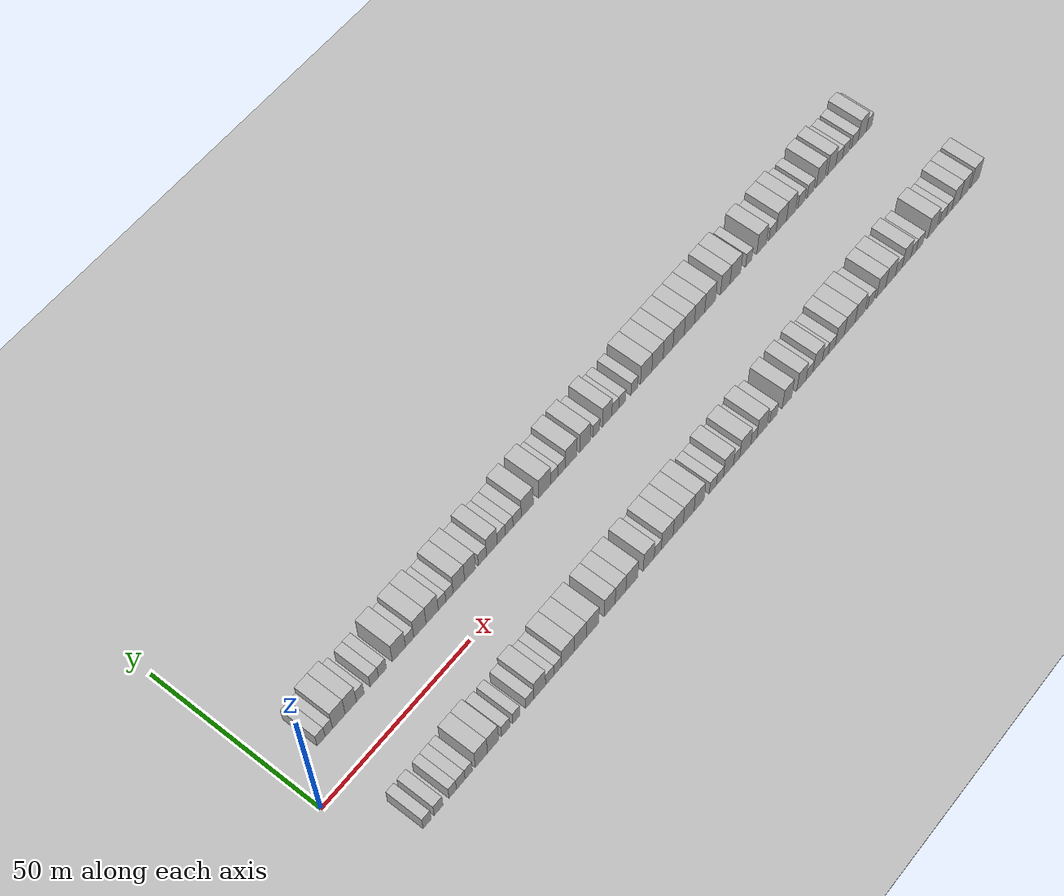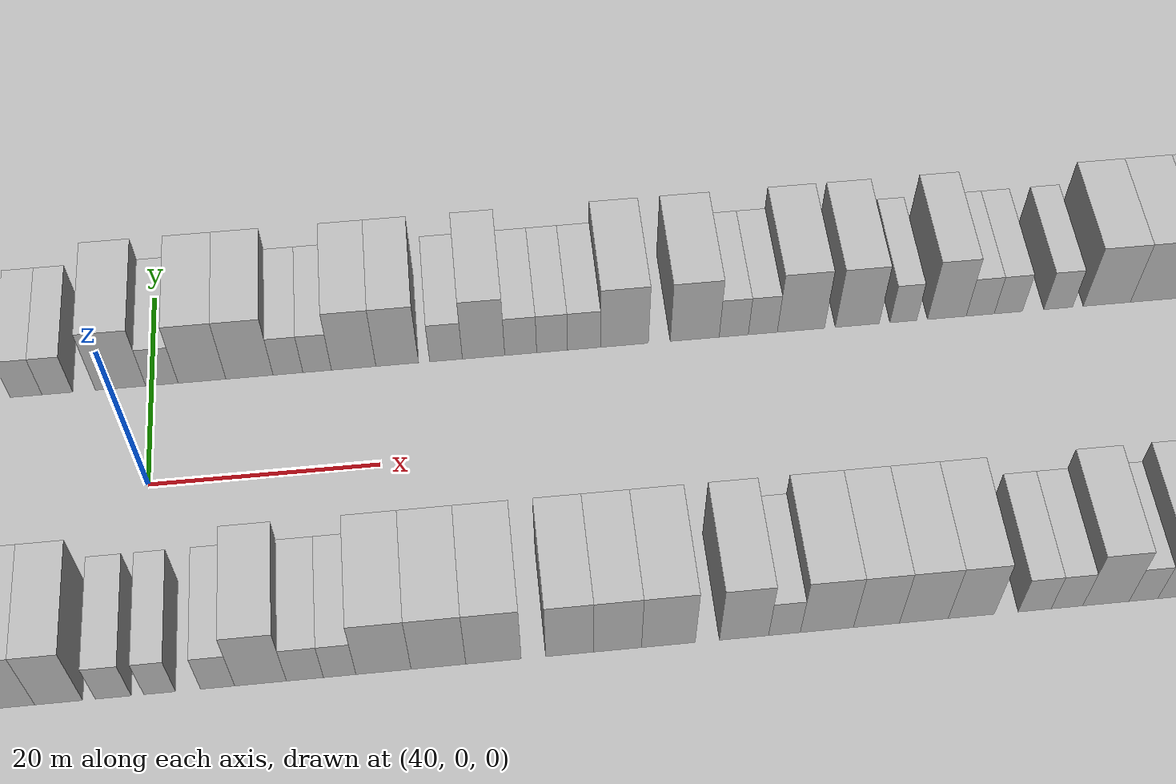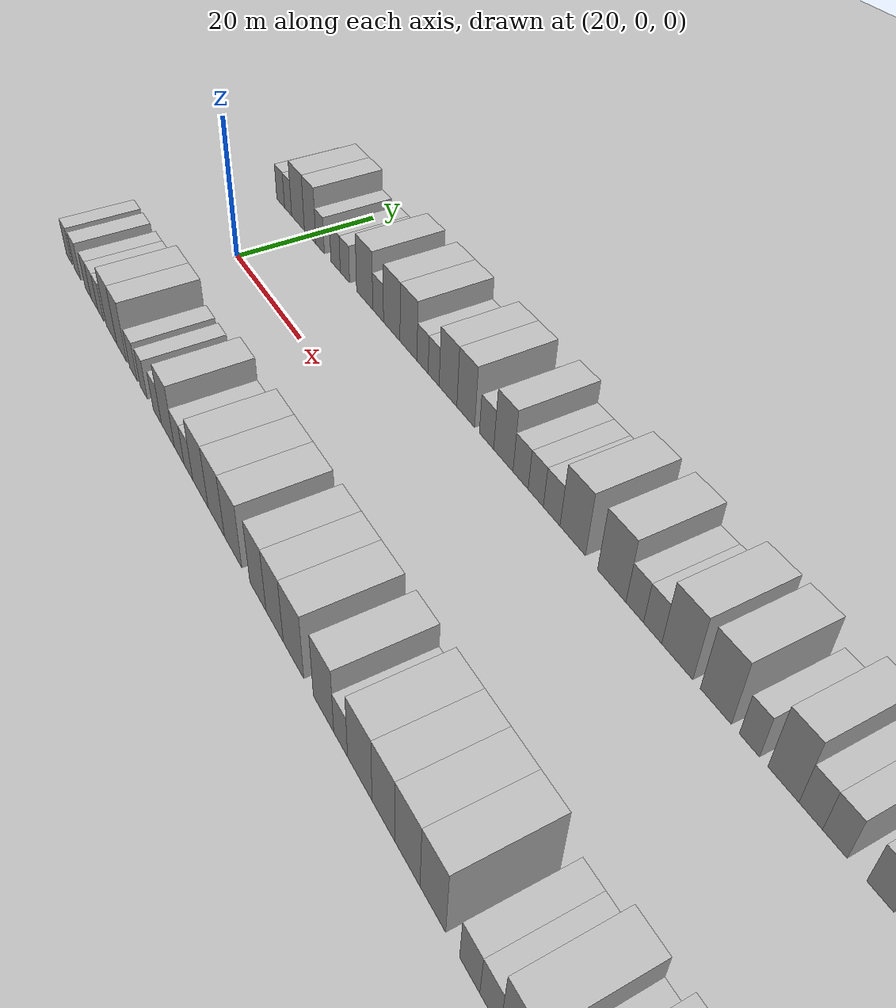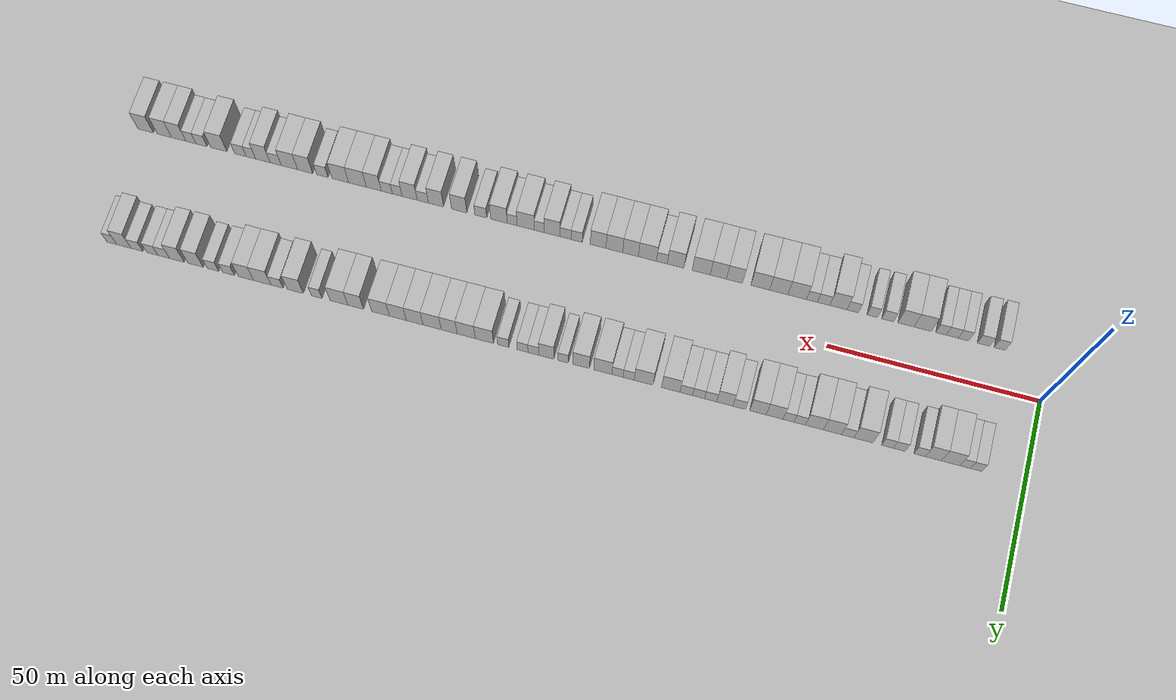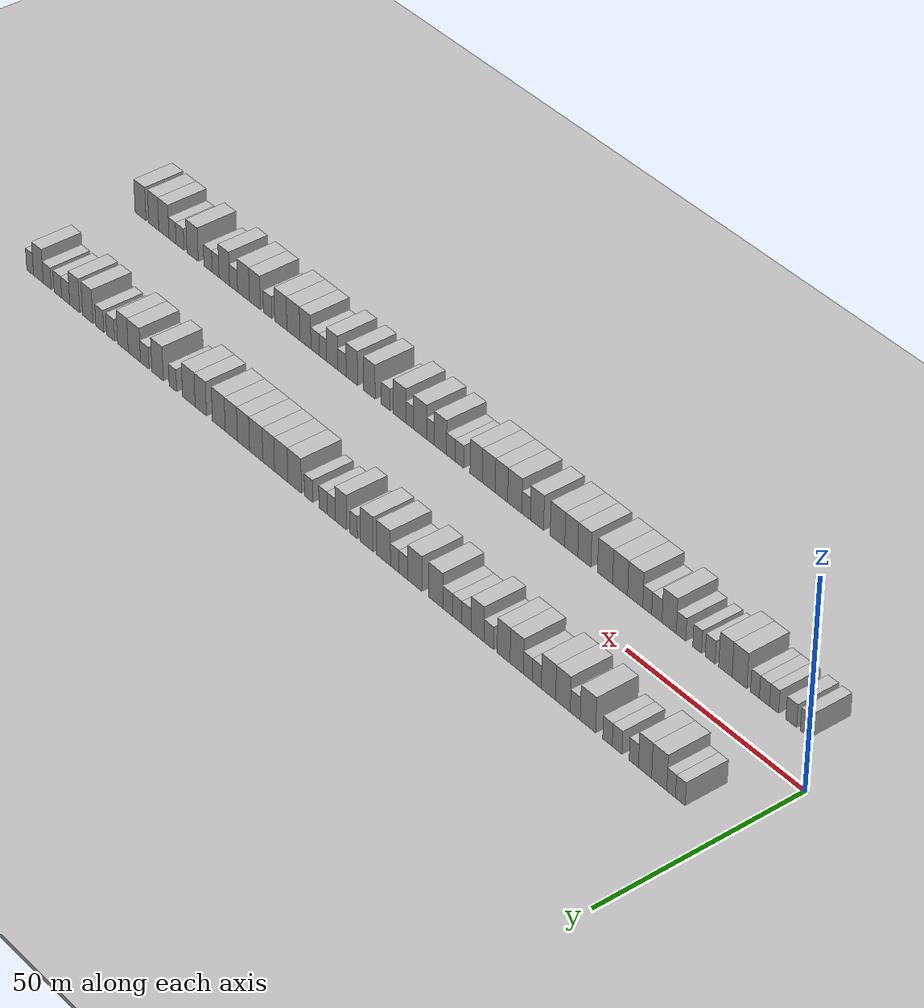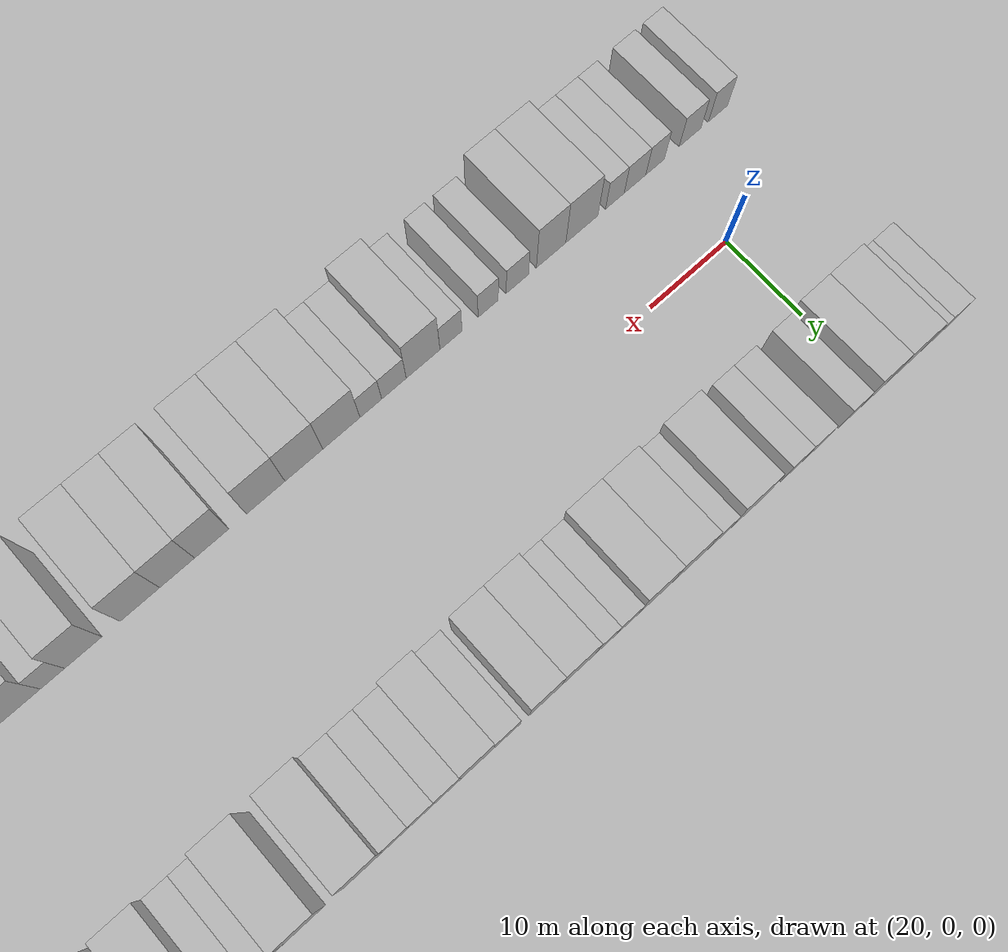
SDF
<?xml version="1.0" encoding="utf-8"?>

<sdf version="1.6">

   <world name="default">

      <gui fullscreen="0">

         <camera name="user_camera">

            <pose>-15 0 4.57585 0 0 0</pose>

            <view_controller>orbit</view_controller>

         </camera>

      </gui>

      <scene>

         <sky>

           <clouds>

             <speed>12</speed>

           </clouds>

         </sky>

         <ambient>0.4 0.4 0.4 1</ambient>

         <background>0.7 0.7 0.7 1</background>

         <shadows>1</shadows>

      </scene>

      <gravity>0 0 -9.8066</gravity>

      <magnetic_field>6e-06 2.3e-05 -4.2e-05</magnetic_field>

      <physics default="0" name="default_physics" type="ode">

         <ode>

            <solver>

               <type>quick</type>

               <iters>10</iters>

               <sor>1.0</sor>

               <use_dynamic_moi_rescaling>0</use_dynamic_moi_rescaling>

            </solver>

            <constraints>

               <cfm>0</cfm>

               <erp>0.2</erp>

               <contact_max_correcting_vel>100</contact_max_correcting_vel>

               <contact_surface_layer>0.001</contact_surface_layer>

            </constraints>

         </ode>

         <max_step_size>0.004</max_step_size>

         <real_time_factor>1</real_time_factor>

         <real_time_update_rate>250</real_time_update_rate>

      </physics>

      <light name="sun" type="directional">

         <cast_shadows>1</cast_shadows>

         <pose>0 0 10 0 0 0</pose>

         <diffuse>0.8 0.8 0.8 1</diffuse>

         <specular>0.2 0.2 0.2 1</specular>

         <attenuation>

            <range>1000</range>

            <constant>0.9</constant>

            <linear>0.01</linear>

            <quadratic>0.001</quadratic>

         </attenuation>

         <direction>-0.5 0.1 -0.9</direction>

      </light>

      <include>

         <name>ground_plane_1</name>

         <uri>model://HANNAS_ground_plane</uri>

         <pose>0 0 0  0 0 0</pose>

      </include>

      <include>

         <name>ground_plane_2</name>

         <uri>model://HANNAS_ground_plane</uri>

         <pose>100 0 0  0 0 0</pose>

      </include>

      <model name="building_1">

         <static>1</static>

         <pose frame="">11.3372 15.0000 0 0.000000 0.000000 1.570796</pose>

         <link name="link">

            <pose frame="">0 0 3.00 0 0 0</pose>

            <collision name="collision">

               <geometry>

                  <box>

                     <size>10.0000 2.6744 6.0000</size>

                  </box>

               </geometry>

               <max_contacts>10</max_contacts>

               <surface>

                  <contact>

                     <ode/>

                  </contact>

                  <bounce/>

                  <friction>

                     <torsional>

                        <ode/>

                     </torsional>

                     <ode/>

                  </friction>

               </surface>

            </collision>

            <visual name="visual">

               <cast_shadows>0</cast_shadows>

               <geometry>

                  <box>

                     <size>10.0000 2.6744 6.0000</size>

                  </box>

               </geometry>

               <material>

                  <script>

                     <uri>model://HANNAS_wall/materials/scripts</uri>

                     <uri>model://HANNAS_wall/materials/textures</uri>

                     <name>vrc/HANNAS_wall</name>

                  </script>

               </material>

            </visual>

            <self_collide>0</self_collide>

            <enable_wind>0</enable_wind>

            <kinematic>0</kinematic>

         </link>

      </model>

      <model name="building_2">

         <static>1</static>

         <pose frame="">13.8785 15.0000 0 0.000000 0.000000 1.570796</pose>

         <link name="link">

            <pose frame="">0 0 3.00 0 0 0</pose>

            <collision name="collision">

               <geometry>

                  <box>

                     <size>10.0000 2.4080 6.0000</size>

                  </box>

               </geometry>

               <max_contacts>10</max_contacts>

               <surface>

                  <contact>

                     <ode/>

                  </contact>

                  <bounce/>

                  <friction>

                     <torsional>

                        <ode/>

                     </torsional>

                     <ode/>

                  </friction>

               </surface>

            </collision>

            <visual name="visual">

               <cast_shadows>0</cast_shadows>

               <geometry>

                  <box>

                     <size>10.0000 2.4080 6.0000</size>

                  </box>

               </geometry>

               <material>

                  <script>

                     <uri>model://HANNAS_wall/materials/scripts</uri>

                     <uri>model://HANNAS_wall/materials/textures</uri>

                     <name>vrc/HANNAS_wall</name>

                  </script>

               </material>

            </visual>

            <self_collide>0</self_collide>

            <enable_wind>0</enable_wind>

            <kinematic>0</kinematic>

         </link>

      </model>

      <model name="building_3">

         <static>1</static>

         <pose frame="">17.1930 15.0000 0 0.000000 0.000000 1.570796</pose>

         <link name="link">

            <pose frame="">0 0 4.50 0 0 0</pose>

            <collision name="collision">

               <geometry>

                  <box>

                     <size>10.0000 4.2211 9.0000</size>

                  </box>

               </geometry>

               <max_contacts>10</max_contacts>

               <surface>

                  <contact>

                     <ode/>

                  </contact>

                  <bounce/>

                  <friction>

                     <torsional>

                        <ode/>

                     </torsional>

                     <ode/>

                  </friction>

               </surface>

            </collision>

            <visual name="visual">

               <cast_shadows>0</cast_shadows>

               <geometry>

                  <box>

                     <size>10.0000 4.2211 9.0000</size>

                  </box>

               </geometry>

               <material>

                  <script>

                     <uri>model://HANNAS_wall/materials/scripts</uri>

                     <uri>model://HANNAS_wall/materials/textures</uri>

                     <name>vrc/HANNAS_wall</name>

                  </script>

               </material>

            </visual>

            <self_collide>0</self_collide>

            <enable_wind>0</enable_wind>

            <kinematic>0</kinematic>

         </link>

      </model>

      <model name="building_4">

         <static>1</static>

         <pose frame="">21.1514 15.0000 0 0.000000 0.000000 1.570796</pose>

         <link name="link">

            <pose frame="">0 0 4.50 0 0 0</pose>

            <collision name="collision">

               <geometry>

                  <box>

                     <size>10.0000 3.6958 9.0000</size>

                  </box>

               </geometry>

               <max_contacts>10</max_contacts>

               <surface>

                  <contact>

                     <ode/>

                  </contact>

                  <bounce/>

                  <friction>

                     <torsional>

                        <ode/>

                     </torsional>

                     <ode/>

                  </friction>

               </surface>

            </collision>

            <visual name="visual">

               <cast_shadows>0</cast_shadows>

               <geometry>

                  <box>

                     <size>10.0000 3.6958 9.0000</size>

                  </box>

               </geometry>

               <material>

                  <script>

                     <uri>model://HANNAS_wall/materials/scripts</uri>

                     <uri>model://HANNAS_wall/materials/textures</uri>

                     <name>vrc/HANNAS_wall</name>

                  </script>

               </material>

            </visual>

            <self_collide>0</self_collide>

            <enable_wind>0</enable_wind>

            <kinematic>0</kinematic>

         </link>

      </model>

      <model name="building_5">

         <static>1</static>

         <pose frame="">24.2985 15.0000 0 0.000000 0.000000 1.570796</pose>

         <link name="link">

            <pose frame="">0 0 3.00 0 0 0</pose>

            <collision name="collision">

               <geometry>

                  <box>

                     <size>10.0000 2.5983 6.0000</size>

                  </box>

               </geometry>

               <max_contacts>10</max_contacts>

               <surface>

                  <contact>

                     <ode/>

                  </contact>

                  <bounce/>

                  <friction>

                     <torsional>

                        <ode/>

                     </torsional>

                     <ode/>

                  </friction>

               </surface>

            </collision>

            <visual name="visual">

               <cast_shadows>0</cast_shadows>

               <geometry>

                  <box>

                     <size>10.0000 2.5983 6.0000</size>

                  </box>

               </geometry>

               <material>

                  <script>

                     <uri>model://HANNAS_wall/materials/scripts</uri>

                     <uri>model://HANNAS_wall/materials/textures</uri>

                     <name>vrc/HANNAS_wall</name>

                  </script>

               </material>

            </visual>

            <self_collide>0</self_collide>

            <enable_wind>0</enable_wind>

            <kinematic>0</kinematic>

         </link>

      </model>

      <model name="building_6">

         <static>1</static>

         <pose frame="">28.9933 15.0000 0 0.000000 0.000000 1.570796</pose>

         <link name="link">

            <pose frame="">0 0 3.00 0 0 0</pose>

            <collision name="collision">

               <geometry>

                  <box>

                     <size>10.0000 2.7913 6.0000</size>

                  </box>

               </geometry>

               <max_contacts>10</max_contacts>

               <surface>

                  <contact>

                     <ode/>

                  </contact>

                  <bounce/>

                  <friction>

                     <torsional>

                        <ode/>

                     </torsional>

                     <ode/>

                  </friction>

               </surface>

            </collision>

            <visual name="visual">

               <cast_shadows>0</cast_shadows>

               <geometry>

                  <box>

                     <size>10.0000 2.7913 6.0000</size>

                  </box>

               </geometry>

               <material>

                  <script>

                     <uri>model://HANNAS_wall/materials/scripts</uri>

                     <uri>model://HANNAS_wall/materials/textures</uri>

                     <name>vrc/HANNAS_wall</name>

                  </script>

               </material>

            </visual>

            <self_collide>0</self_collide>

            <enable_wind>0</enable_wind>

            <kinematic>0</kinematic>

         </link>

      </model>

      <model name="building_7">

         <static>1</static>

         <pose frame="">31.7404 15.0000 0 0.000000 0.000000 1.570796</pose>

         <link name="link">

            <pose frame="">0 0 3.00 0 0 0</pose>

            <collision name="collision">

               <geometry>

                  <box>

                     <size>10.0000 2.7030 6.0000</size>

                  </box>

               </geometry>

               <max_contacts>10</max_contacts>

               <surface>

                  <contact>

                     <ode/>

                  </contact>

                  <bounce/>

                  <friction>

                     <torsional>

                        <ode/>

                     </torsional>

                     <ode/>

                  </friction>

               </surface>

            </collision>

            <visual name="visual">

               <cast_shadows>0</cast_shadows>

               <geometry>

                  <box>

                     <size>10.0000 2.7030 6.0000</size>

                  </box>

               </geometry>

               <material>

                  <script>

                     <uri>model://HANNAS_wall/materials/scripts</uri>

                     <uri>model://HANNAS_wall/materials/textures</uri>

                     <name>vrc/HANNAS_wall</name>

                  </script>

               </material>

            </visual>

            <self_collide>0</self_collide>

            <enable_wind>0</enable_wind>

            <kinematic>0</kinematic>

         </link>

      </model>

      <model name="building_8">

         <static>1</static>

         <pose frame="">37.3140 15.0000 0 0.000000 0.000000 1.570796</pose>

         <link name="link">

            <pose frame="">0 0 4.50 0 0 0</pose>

            <collision name="collision">

               <geometry>

                  <box>

                     <size>10.0000 4.4440 9.0000</size>

                  </box>

               </geometry>

               <max_contacts>10</max_contacts>

               <surface>

                  <contact>

                     <ode/>

                  </contact>

                  <bounce/>

                  <friction>

                     <torsional>

                        <ode/>

                     </torsional>

                     <ode/>

                  </friction>

               </surface>

            </collision>

            <visual name="visual">

               <cast_shadows>0</cast_shadows>

               <geometry>

                  <box>

                     <size>10.0000 4.4440 9.0000</size>

                  </box>

               </geometry>

               <material>

                  <script>

                     <uri>model://HANNAS_wall/materials/scripts</uri>

                     <uri>model://HANNAS_wall/materials/textures</uri>

                     <name>vrc/HANNAS_wall</name>

                  </script>

               </material>

            </visual>

            <self_collide>0</self_collide>

            <enable_wind>0</enable_wind>

            <kinematic>0</kinematic>

         </link>

      </model>

      <model name="building_9">

         <static>1</static>

         <pose frame="">40.9731 15.0000 0 0.000000 0.000000 1.570796</pose>

         <link name="link">

            <pose frame="">0 0 3.00 0 0 0</pose>

            <collision name="collision">

               <geometry>

                  <box>

                     <size>10.0000 2.8742 6.0000</size>

                  </box>

               </geometry>

               <max_contacts>10</max_contacts>

               <surface>

                  <contact>

                     <ode/>

                  </contact>

                  <bounce/>

                  <friction>

                     <torsional>

                        <ode/>

                     </torsional>

                     <ode/>

                  </friction>

               </surface>

            </collision>

            <visual name="visual">

               <cast_shadows>0</cast_shadows>

               <geometry>

                  <box>

                     <size>10.0000 2.8742 6.0000</size>

                  </box>

               </geometry>

               <material>

                  <script>

                     <uri>model://HANNAS_wall/materials/scripts</uri>

                     <uri>model://HANNAS_wall/materials/textures</uri>

                     <name>vrc/HANNAS_wall</name>

                  </script>

               </material>

            </visual>

            <self_collide>0</self_collide>

            <enable_wind>0</enable_wind>

            <kinematic>0</kinematic>

         </link>

      </model>

      <model name="building_10">

         <static>1</static>

         <pose frame="">44.5333 15.0000 0 0.000000 0.000000 1.570796</pose>

         <link name="link">

            <pose frame="">0 0 4.50 0 0 0</pose>

            <collision name="collision">

               <geometry>

                  <box>

                     <size>10.0000 4.2464 9.0000</size>

                  </box>

               </geometry>

               <max_contacts>10</max_contacts>

               <surface>

                  <contact>

                     <ode/>

                  </contact>

                  <bounce/>

                  <friction>

                     <torsional>

                        <ode/>

                     </torsional>

                     <ode/>

                  </friction>

               </surface>

            </collision>

            <visual name="visual">

               <cast_shadows>0</cast_shadows>

               <geometry>

                  <box>

                     <size>10.0000 4.2464 9.0000</size>

                  </box>

               </geometry>

               <material>

                  <script>

                     <uri>model://HANNAS_wall/materials/scripts</uri>

                     <uri>model://HANNAS_wall/materials/textures</uri>

                     <name>vrc/HANNAS_wall</name>

                  </script>

               </material>

            </visual>

            <self_collide>0</self_collide>

            <enable_wind>0</enable_wind>

            <kinematic>0</kinematic>

         </link>

      </model>

      <model name="building_11">

         <static>1</static>

         <pose frame="">48.7557 15.0000 0 0.000000 0.000000 1.570796</pose>

         <link name="link">

            <pose frame="">0 0 4.50 0 0 0</pose>

            <collision name="collision">

               <geometry>

                  <box>

                     <size>10.0000 4.1984 9.0000</size>

                  </box>

               </geometry>

               <max_contacts>10</max_contacts>

               <surface>

                  <contact>

                     <ode/>

                  </contact>

                  <bounce/>

                  <friction>

                     <torsional>

                        <ode/>

                     </torsional>

                     <ode/>

                  </friction>

               </surface>

            </collision>

            <visual name="visual">

               <cast_shadows>0</cast_shadows>

               <geometry>

                  <box>

                     <size>10.0000 4.1984 9.0000</size>

                  </box>

               </geometry>

               <material>

                  <script>

                     <uri>model://HANNAS_wall/materials/scripts</uri>

                     <uri>model://HANNAS_wall/materials/textures</uri>

                     <name>vrc/HANNAS_wall</name>

                  </script>

               </material>

            </visual>

            <self_collide>0</self_collide>

            <enable_wind>0</enable_wind>

            <kinematic>0</kinematic>

         </link>

      </model>

      <model name="building_12">

         <static>1</static>

         <pose frame="">52.1893 15.0000 0 0.000000 0.000000 1.570796</pose>

         <link name="link">

            <pose frame="">0 0 3.00 0 0 0</pose>

            <collision name="collision">

               <geometry>

                  <box>

                     <size>10.0000 2.6688 6.0000</size>

                  </box>

               </geometry>

               <max_contacts>10</max_contacts>

               <surface>

                  <contact>

                     <ode/>

                  </contact>

                  <bounce/>

                  <friction>

                     <torsional>

                        <ode/>

                     </torsional>

                     <ode/>

                  </friction>

               </surface>

            </collision>

            <visual name="visual">

               <cast_shadows>0</cast_shadows>

               <geometry>

                  <box>

                     <size>10.0000 2.6688 6.0000</size>

                  </box>

               </geometry>

               <material>

                  <script>

                     <uri>model://HANNAS_wall/materials/scripts</uri>

                     <uri>model://HANNAS_wall/materials/textures</uri>

                     <name>vrc/HANNAS_wall</name>

                  </script>

               </material>

            </visual>

            <self_collide>0</self_collide>

            <enable_wind>0</enable_wind>

            <kinematic>0</kinematic>

         </link>

      </model>

      <model name="building_13">

         <static>1</static>

         <pose frame="">54.8003 15.0000 0 0.000000 0.000000 1.570796</pose>

         <link name="link">

            <pose frame="">0 0 3.00 0 0 0</pose>

            <collision name="collision">

               <geometry>

                  <box>

                     <size>10.0000 2.5532 6.0000</size>

                  </box>

               </geometry>

               <max_contacts>10</max_contacts>

               <surface>

                  <contact>

                     <ode/>

                  </contact>

                  <bounce/>

                  <friction>

                     <torsional>

                        <ode/>

                     </torsional>

                     <ode/>

                  </friction>

               </surface>

            </collision>

            <visual name="visual">

               <cast_shadows>0</cast_shadows>

               <geometry>

                  <box>

                     <size>10.0000 2.5532 6.0000</size>

                  </box>

               </geometry>

               <material>

                  <script>

                     <uri>model://HANNAS_wall/materials/scripts</uri>

                     <uri>model://HANNAS_wall/materials/textures</uri>

                     <name>vrc/HANNAS_wall</name>

                  </script>

               </material>

            </visual>

            <self_collide>0</self_collide>

            <enable_wind>0</enable_wind>

            <kinematic>0</kinematic>

         </link>

      </model>

      <model name="building_14">

         <static>1</static>

         <pose frame="">58.0679 15.0000 0 0.000000 0.000000 1.570796</pose>

         <link name="link">

            <pose frame="">0 0 4.50 0 0 0</pose>

            <collision name="collision">

               <geometry>

                  <box>

                     <size>10.0000 3.9819 9.0000</size>

                  </box>

               </geometry>

               <max_contacts>10</max_contacts>

               <surface>

                  <contact>

                     <ode/>

                  </contact>

                  <bounce/>

                  <friction>

                     <torsional>

                        <ode/>

                     </torsional>

                     <ode/>

                  </friction>

               </surface>

            </collision>

            <visual name="visual">

               <cast_shadows>0</cast_shadows>

               <geometry>

                  <box>

                     <size>10.0000 3.9819 9.0000</size>

                  </box>

               </geometry>

               <material>

                  <script>

                     <uri>model://HANNAS_wall/materials/scripts</uri>

                     <uri>model://HANNAS_wall/materials/textures</uri>

                     <name>vrc/HANNAS_wall</name>

                  </script>

               </material>

            </visual>

            <self_collide>0</self_collide>

            <enable_wind>0</enable_wind>

            <kinematic>0</kinematic>

         </link>

      </model>

      <model name="building_15">

         <static>1</static>

         <pose frame="">61.9804 15.0000 0 0.000000 0.000000 1.570796</pose>

         <link name="link">

            <pose frame="">0 0 4.50 0 0 0</pose>

            <collision name="collision">

               <geometry>

                  <box>

                     <size>10.0000 3.8432 9.0000</size>

                  </box>

               </geometry>

               <max_contacts>10</max_contacts>

               <surface>

                  <contact>

                     <ode/>

                  </contact>

                  <bounce/>

                  <friction>

                     <torsional>

                        <ode/>

                     </torsional>

                     <ode/>

                  </friction>

               </surface>

            </collision>

            <visual name="visual">

               <cast_shadows>0</cast_shadows>

               <geometry>

                  <box>

                     <size>10.0000 3.8432 9.0000</size>

                  </box>

               </geometry>

               <material>

                  <script>

                     <uri>model://HANNAS_wall/materials/scripts</uri>

                     <uri>model://HANNAS_wall/materials/textures</uri>

                     <name>vrc/HANNAS_wall</name>

                  </script>

               </material>

            </visual>

            <self_collide>0</self_collide>

            <enable_wind>0</enable_wind>

            <kinematic>0</kinematic>

         </link>

      </model>

      <model name="building_16">

         <static>1</static>

         <pose frame="">66.3748 15.0000 0 0.000000 0.000000 1.570796</pose>

         <link name="link">

            <pose frame="">0 0 3.00 0 0 0</pose>

            <collision name="collision">

               <geometry>

                  <box>

                     <size>10.0000 2.9455 6.0000</size>

                  </box>

               </geometry>

               <max_contacts>10</max_contacts>

               <surface>

                  <contact>

                     <ode/>

                  </contact>

                  <bounce/>

                  <friction>

                     <torsional>

                        <ode/>

                     </torsional>

                     <ode/>

                  </friction>

               </surface>

            </collision>

            <visual name="visual">

               <cast_shadows>0</cast_shadows>

               <geometry>

                  <box>

                     <size>10.0000 2.9455 6.0000</size>

                  </box>

               </geometry>

               <material>

                  <script>

                     <uri>model://HANNAS_wall/materials/scripts</uri>

                     <uri>model://HANNAS_wall/materials/textures</uri>

                     <name>vrc/HANNAS_wall</name>

                  </script>

               </material>

            </visual>

            <self_collide>0</self_collide>

            <enable_wind>0</enable_wind>

            <kinematic>0</kinematic>

         </link>

      </model>

      <model name="building_17">

         <static>1</static>

         <pose frame="">69.7596 15.0000 0 0.000000 0.000000 1.570796</pose>

         <link name="link">

            <pose frame="">0 0 4.50 0 0 0</pose>

            <collision name="collision">

               <geometry>

                  <box>

                     <size>10.0000 3.8243 9.0000</size>

                  </box>

               </geometry>

               <max_contacts>10</max_contacts>

               <surface>

                  <contact>

                     <ode/>

                  </contact>

                  <bounce/>

                  <friction>

                     <torsional>

                        <ode/>

                     </torsional>

                     <ode/>

                  </friction>

               </surface>

            </collision>

            <visual name="visual">

               <cast_shadows>0</cast_shadows>

               <geometry>

                  <box>

                     <size>10.0000 3.8243 9.0000</size>

                  </box>

               </geometry>

               <material>

                  <script>

                     <uri>model://HANNAS_wall/materials/scripts</uri>

                     <uri>model://HANNAS_wall/materials/textures</uri>

                     <name>vrc/HANNAS_wall</name>

                  </script>

               </material>

            </visual>

            <self_collide>0</self_collide>

            <enable_wind>0</enable_wind>

            <kinematic>0</kinematic>

         </link>

      </model>

      <model name="building_18">

         <static>1</static>

         <pose frame="">73.1181 15.0000 0 0.000000 0.000000 1.570796</pose>

         <link name="link">

            <pose frame="">0 0 3.00 0 0 0</pose>

            <collision name="collision">

               <geometry>

                  <box>

                     <size>10.0000 2.8927 6.0000</size>

                  </box>

               </geometry>

               <max_contacts>10</max_contacts>

               <surface>

                  <contact>

                     <ode/>

                  </contact>

                  <bounce/>

                  <friction>

                     <torsional>

                        <ode/>

                     </torsional>

                     <ode/>

                  </friction>

               </surface>

            </collision>

            <visual name="visual">

               <cast_shadows>0</cast_shadows>

               <geometry>

                  <box>

                     <size>10.0000 2.8927 6.0000</size>

                  </box>

               </geometry>

               <material>

                  <script>

                     <uri>model://HANNAS_wall/materials/scripts</uri>

                     <uri>model://HANNAS_wall/materials/textures</uri>

                     <name>vrc/HANNAS_wall</name>

                  </script>

               </material>

            </visual>

            <self_collide>0</self_collide>

            <enable_wind>0</enable_wind>

            <kinematic>0</kinematic>

         </link>

      </model>

      <model name="building_19">

         <static>1</static>

         <pose frame="">75.9669 15.0000 0 0.000000 0.000000 1.570796</pose>

         <link name="link">

            <pose frame="">0 0 3.00 0 0 0</pose>

            <collision name="collision">

               <geometry>

                  <box>

                     <size>10.0000 2.8049 6.0000</size>

                  </box>

               </geometry>

               <max_contacts>10</max_contacts>

               <surface>

                  <contact>

                     <ode/>

                  </contact>

                  <bounce/>

                  <friction>

                     <torsional>

                        <ode/>

                     </torsional>

                     <ode/>

                  </friction>

               </surface>

            </collision>

            <visual name="visual">

               <cast_shadows>0</cast_shadows>

               <geometry>

                  <box>

                     <size>10.0000 2.8049 6.0000</size>

                  </box>

               </geometry>

               <material>

                  <script>

                     <uri>model://HANNAS_wall/materials/scripts</uri>

                     <uri>model://HANNAS_wall/materials/textures</uri>

                     <name>vrc/HANNAS_wall</name>

                  </script>

               </material>

            </visual>

            <self_collide>0</self_collide>

            <enable_wind>0</enable_wind>

            <kinematic>0</kinematic>

         </link>

      </model>

      <model name="building_20">

         <static>1</static>

         <pose frame="">78.8637 15.0000 0 0.000000 0.000000 1.570796</pose>

         <link name="link">

            <pose frame="">0 0 3.00 0 0 0</pose>

            <collision name="collision">

               <geometry>

                  <box>

                     <size>10.0000 2.9887 6.0000</size>

                  </box>

               </geometry>

               <max_contacts>10</max_contacts>

               <surface>

                  <contact>

                     <ode/>

                  </contact>

                  <bounce/>

                  <friction>

                     <torsional>

                        <ode/>

                     </torsional>

                     <ode/>

                  </friction>

               </surface>

            </collision>

            <visual name="visual">

               <cast_shadows>0</cast_shadows>

               <geometry>

                  <box>

                     <size>10.0000 2.9887 6.0000</size>

                  </box>

               </geometry>

               <material>

                  <script>

                     <uri>model://HANNAS_wall/materials/scripts</uri>

                     <uri>model://HANNAS_wall/materials/textures</uri>

                     <name>vrc/HANNAS_wall</name>

                  </script>

               </material>

            </visual>

            <self_collide>0</self_collide>

            <enable_wind>0</enable_wind>

            <kinematic>0</kinematic>

         </link>

      </model>

      <model name="building_21">

         <static>1</static>

         <pose frame="">82.5431 15.0000 0 0.000000 0.000000 1.570796</pose>

         <link name="link">

            <pose frame="">0 0 4.50 0 0 0</pose>

            <collision name="collision">

               <geometry>

                  <box>

                     <size>10.0000 4.3702 9.0000</size>

                  </box>

               </geometry>

               <max_contacts>10</max_contacts>

               <surface>

                  <contact>

                     <ode/>

                  </contact>

                  <bounce/>

                  <friction>

                     <torsional>

                        <ode/>

                     </torsional>

                     <ode/>

                  </friction>

               </surface>

            </collision>

            <visual name="visual">

               <cast_shadows>0</cast_shadows>

               <geometry>

                  <box>

                     <size>10.0000 4.3702 9.0000</size>

                  </box>

               </geometry>

               <material>

                  <script>

                     <uri>model://HANNAS_wall/materials/scripts</uri>

                     <uri>model://HANNAS_wall/materials/textures</uri>

                     <name>vrc/HANNAS_wall</name>

                  </script>

               </material>

            </visual>

            <self_collide>0</self_collide>

            <enable_wind>0</enable_wind>

            <kinematic>0</kinematic>

         </link>

      </model>

      <model name="building_22">

         <static>1</static>

         <pose frame="">88.9695 15.0000 0 0.000000 0.000000 1.570796</pose>

         <link name="link">

            <pose frame="">0 0 4.50 0 0 0</pose>

            <collision name="collision">

               <geometry>

                  <box>

                     <size>10.0000 4.4826 9.0000</size>

                  </box>

               </geometry>

               <max_contacts>10</max_contacts>

               <surface>

                  <contact>

                     <ode/>

                  </contact>

                  <bounce/>

                  <friction>

                     <torsional>

                        <ode/>

                     </torsional>

                     <ode/>

                  </friction>

               </surface>

            </collision>

            <visual name="visual">

               <cast_shadows>0</cast_shadows>

               <geometry>

                  <box>

                     <size>10.0000 4.4826 9.0000</size>

                  </box>

               </geometry>

               <material>

                  <script>

                     <uri>model://HANNAS_wall/materials/scripts</uri>

                     <uri>model://HANNAS_wall/materials/textures</uri>

                     <name>vrc/HANNAS_wall</name>

                  </script>

               </material>

            </visual>

            <self_collide>0</self_collide>

            <enable_wind>0</enable_wind>

            <kinematic>0</kinematic>

         </link>

      </model>

      <model name="building_23">

         <static>1</static>

         <pose frame="">92.5445 15.0000 0 0.000000 0.000000 1.570796</pose>

         <link name="link">

            <pose frame="">0 0 3.00 0 0 0</pose>

            <collision name="collision">

               <geometry>

                  <box>

                     <size>10.0000 2.6674 6.0000</size>

                  </box>

               </geometry>

               <max_contacts>10</max_contacts>

               <surface>

                  <contact>

                     <ode/>

                  </contact>

                  <bounce/>

                  <friction>

                     <torsional>

                        <ode/>

                     </torsional>

                     <ode/>

                  </friction>

               </surface>

            </collision>

            <visual name="visual">

               <cast_shadows>0</cast_shadows>

               <geometry>

                  <box>

                     <size>10.0000 2.6674 6.0000</size>

                  </box>

               </geometry>

               <material>

                  <script>

                     <uri>model://HANNAS_wall/materials/scripts</uri>

                     <uri>model://HANNAS_wall/materials/textures</uri>

                     <name>vrc/HANNAS_wall</name>

                  </script>

               </material>

            </visual>

            <self_collide>0</self_collide>

            <enable_wind>0</enable_wind>

            <kinematic>0</kinematic>

         </link>

      </model>

      <model name="building_24">

         <static>1</static>

         <pose frame="">95.2123 15.0000 0 0.000000 0.000000 1.570796</pose>

         <link name="link">

            <pose frame="">0 0 3.00 0 0 0</pose>

            <collision name="collision">

               <geometry>

                  <box>

                     <size>10.0000 2.6682 6.0000</size>

                  </box>

               </geometry>

               <max_contacts>10</max_contacts>

               <surface>

                  <contact>

                     <ode/>

                  </contact>

                  <bounce/>

                  <friction>

                     <torsional>

                        <ode/>

                     </torsional>

                     <ode/>

                  </friction>

               </surface>

            </collision>

            <visual name="visual">

               <cast_shadows>0</cast_shadows>

               <geometry>

                  <box>

                     <size>10.0000 2.6682 6.0000</size>

                  </box>

               </geometry>

               <material>

                  <script>

                     <uri>model://HANNAS_wall/materials/scripts</uri>

                     <uri>model://HANNAS_wall/materials/textures</uri>

                     <name>vrc/HANNAS_wall</name>

                  </script>

               </material>

            </visual>

            <self_collide>0</self_collide>

            <enable_wind>0</enable_wind>

            <kinematic>0</kinematic>

         </link>

      </model>

      <model name="building_25">

         <static>1</static>

         <pose frame="">98.7237 15.0000 0 0.000000 0.000000 1.570796</pose>

         <link name="link">

            <pose frame="">0 0 4.50 0 0 0</pose>

            <collision name="collision">

               <geometry>

                  <box>

                     <size>10.0000 4.3547 9.0000</size>

                  </box>

               </geometry>

               <max_contacts>10</max_contacts>

               <surface>

                  <contact>

                     <ode/>

                  </contact>

                  <bounce/>

                  <friction>

                     <torsional>

                        <ode/>

                     </torsional>

                     <ode/>

                  </friction>

               </surface>

            </collision>

            <visual name="visual">

               <cast_shadows>0</cast_shadows>

               <geometry>

                  <box>

                     <size>10.0000 4.3547 9.0000</size>

                  </box>

               </geometry>

               <material>

                  <script>

                     <uri>model://HANNAS_wall/materials/scripts</uri>

                     <uri>model://HANNAS_wall/materials/textures</uri>

                     <name>vrc/HANNAS_wall</name>

                  </script>

               </material>

            </visual>

            <self_collide>0</self_collide>

            <enable_wind>0</enable_wind>

            <kinematic>0</kinematic>

         </link>

      </model>

      <model name="building_26">

         <static>1</static>

         <pose frame="">103.9300 15.0000 0 0.000000 0.000000 1.570796</pose>

         <link name="link">

            <pose frame="">0 0 4.50 0 0 0</pose>

            <collision name="collision">

               <geometry>

                  <box>

                     <size>10.0000 4.0577 9.0000</size>

                  </box>

               </geometry>

               <max_contacts>10</max_contacts>

               <surface>

                  <contact>

                     <ode/>

                  </contact>

                  <bounce/>

                  <friction>

                     <torsional>

                        <ode/>

                     </torsional>

                     <ode/>

                  </friction>

               </surface>

            </collision>

            <visual name="visual">

               <cast_shadows>0</cast_shadows>

               <geometry>

                  <box>

                     <size>10.0000 4.0577 9.0000</size>

                  </box>

               </geometry>

               <material>

                  <script>

                     <uri>model://HANNAS_wall/materials/scripts</uri>

                     <uri>model://HANNAS_wall/materials/textures</uri>

                     <name>vrc/HANNAS_wall</name>

                  </script>

               </material>

            </visual>

            <self_collide>0</self_collide>

            <enable_wind>0</enable_wind>

            <kinematic>0</kinematic>

         </link>

      </model>

      <model name="building_27">

         <static>1</static>

         <pose frame="">108.2009 15.0000 0 0.000000 0.000000 1.570796</pose>

         <link name="link">

            <pose frame="">0 0 3.00 0 0 0</pose>

            <collision name="collision">

               <geometry>

                  <box>

                     <size>10.0000 2.4841 6.0000</size>

                  </box>

               </geometry>

               <max_contacts>10</max_contacts>

               <surface>

                  <contact>

                     <ode/>

                  </contact>

                  <bounce/>

                  <friction>

                     <torsional>

                        <ode/>

                     </torsional>

                     <ode/>

                  </friction>

               </surface>

            </collision>

            <visual name="visual">

               <cast_shadows>0</cast_shadows>

               <geometry>

                  <box>

                     <size>10.0000 2.4841 6.0000</size>

                  </box>

               </geometry>

               <material>

                  <script>

                     <uri>model://HANNAS_wall/materials/scripts</uri>

                     <uri>model://HANNAS_wall/materials/textures</uri>

                     <name>vrc/HANNAS_wall</name>

                  </script>

               </material>

            </visual>

            <self_collide>0</self_collide>

            <enable_wind>0</enable_wind>

            <kinematic>0</kinematic>

         </link>

      </model>

      <model name="building_28">

         <static>1</static>

         <pose frame="">112.2435 15.0000 0 0.000000 0.000000 1.570796</pose>

         <link name="link">

            <pose frame="">0 0 4.50 0 0 0</pose>

            <collision name="collision">

               <geometry>

                  <box>

                     <size>10.0000 3.6010 9.0000</size>

                  </box>

               </geometry>

               <max_contacts>10</max_contacts>

               <surface>

                  <contact>

                     <ode/>

                  </contact>

                  <bounce/>

                  <friction>

                     <torsional>

                        <ode/>

                     </torsional>

                     <ode/>

                  </friction>

               </surface>

            </collision>

            <visual name="visual">

               <cast_shadows>0</cast_shadows>

               <geometry>

                  <box>

                     <size>10.0000 3.6010 9.0000</size>

                  </box>

               </geometry>

               <material>

                  <script>

                     <uri>model://HANNAS_wall/materials/scripts</uri>

                     <uri>model://HANNAS_wall/materials/textures</uri>

                     <name>vrc/HANNAS_wall</name>

                  </script>

               </material>

            </visual>

            <self_collide>0</self_collide>

            <enable_wind>0</enable_wind>

            <kinematic>0</kinematic>

         </link>

      </model>

      <model name="building_29">

         <static>1</static>

         <pose frame="">115.3490 15.0000 0 0.000000 0.000000 1.570796</pose>

         <link name="link">

            <pose frame="">0 0 3.00 0 0 0</pose>

            <collision name="collision">

               <geometry>

                  <box>

                     <size>10.0000 2.6100 6.0000</size>

                  </box>

               </geometry>

               <max_contacts>10</max_contacts>

               <surface>

                  <contact>

                     <ode/>

                  </contact>

                  <bounce/>

                  <friction>

                     <torsional>

                        <ode/>

                     </torsional>

                     <ode/>

                  </friction>

               </surface>

            </collision>

            <visual name="visual">

               <cast_shadows>0</cast_shadows>

               <geometry>

                  <box>

                     <size>10.0000 2.6100 6.0000</size>

                  </box>

               </geometry>

               <material>

                  <script>

                     <uri>model://HANNAS_wall/materials/scripts</uri>

                     <uri>model://HANNAS_wall/materials/textures</uri>

                     <name>vrc/HANNAS_wall</name>

                  </script>

               </material>

            </visual>

            <self_collide>0</self_collide>

            <enable_wind>0</enable_wind>

            <kinematic>0</kinematic>

         </link>

      </model>

      <model name="building_30">

         <static>1</static>

         <pose frame="">117.9736 15.0000 0 0.000000 0.000000 1.570796</pose>

         <link name="link">

            <pose frame="">0 0 3.00 0 0 0</pose>

            <collision name="collision">

               <geometry>

                  <box>

                     <size>10.0000 2.6391 6.0000</size>

                  </box>

               </geometry>

               <max_contacts>10</max_contacts>

               <surface>

                  <contact>

                     <ode/>

                  </contact>

                  <bounce/>

                  <friction>

                     <torsional>

                        <ode/>

                     </torsional>

                     <ode/>

                  </friction>

               </surface>

            </collision>

            <visual name="visual">

               <cast_shadows>0</cast_shadows>

               <geometry>

                  <box>

                     <size>10.0000 2.6391 6.0000</size>

                  </box>

               </geometry>

               <material>

                  <script>

                     <uri>model://HANNAS_wall/materials/scripts</uri>

                     <uri>model://HANNAS_wall/materials/textures</uri>

                     <name>vrc/HANNAS_wall</name>

                  </script>

               </material>

            </visual>

            <self_collide>0</self_collide>

            <enable_wind>0</enable_wind>

            <kinematic>0</kinematic>

         </link>

      </model>

      <model name="building_31">

         <static>1</static>

         <pose frame="">122.6440 15.0000 0 0.000000 0.000000 1.570796</pose>

         <link name="link">

            <pose frame="">0 0 3.00 0 0 0</pose>

            <collision name="collision">

               <geometry>

                  <box>

                     <size>10.0000 2.7017 6.0000</size>

                  </box>

               </geometry>

               <max_contacts>10</max_contacts>

               <surface>

                  <contact>

                     <ode/>

                  </contact>

                  <bounce/>

                  <friction>

                     <torsional>

                        <ode/>

                     </torsional>

                     <ode/>

                  </friction>

               </surface>

            </collision>

            <visual name="visual">

               <cast_shadows>0</cast_shadows>

               <geometry>

                  <box>

                     <size>10.0000 2.7017 6.0000</size>

                  </box>

               </geometry>

               <material>

                  <script>

                     <uri>model://HANNAS_wall/materials/scripts</uri>

                     <uri>model://HANNAS_wall/materials/textures</uri>

                     <name>vrc/HANNAS_wall</name>

                  </script>

               </material>

            </visual>

            <self_collide>0</self_collide>

            <enable_wind>0</enable_wind>

            <kinematic>0</kinematic>

         </link>

      </model>

      <model name="building_32">

         <static>1</static>

         <pose frame="">127.2096 15.0000 0 0.000000 0.000000 1.570796</pose>

         <link name="link">

            <pose frame="">0 0 4.50 0 0 0</pose>

            <collision name="collision">

               <geometry>

                  <box>

                     <size>10.0000 4.4295 9.0000</size>

                  </box>

               </geometry>

               <max_contacts>10</max_contacts>

               <surface>

                  <contact>

                     <ode/>

                  </contact>

                  <bounce/>

                  <friction>

                     <torsional>

                        <ode/>

                     </torsional>

                     <ode/>

                  </friction>

               </surface>

            </collision>

            <visual name="visual">

               <cast_shadows>0</cast_shadows>

               <geometry>

                  <box>

                     <size>10.0000 4.4295 9.0000</size>

                  </box>

               </geometry>

               <material>

                  <script>

                     <uri>model://HANNAS_wall/materials/scripts</uri>

                     <uri>model://HANNAS_wall/materials/textures</uri>

                     <name>vrc/HANNAS_wall</name>

                  </script>

               </material>

            </visual>

            <self_collide>0</self_collide>

            <enable_wind>0</enable_wind>

            <kinematic>0</kinematic>

         </link>

      </model>

      <model name="building_33">

         <static>1</static>

         <pose frame="">131.6204 15.0000 0 0.000000 0.000000 1.570796</pose>

         <link name="link">

            <pose frame="">0 0 4.50 0 0 0</pose>

            <collision name="collision">

               <geometry>

                  <box>

                     <size>10.0000 4.3922 9.0000</size>

                  </box>

               </geometry>

               <max_contacts>10</max_contacts>

               <surface>

                  <contact>

                     <ode/>

                  </contact>

                  <bounce/>

                  <friction>

                     <torsional>

                        <ode/>

                     </torsional>

                     <ode/>

                  </friction>

               </surface>

            </collision>

            <visual name="visual">

               <cast_shadows>0</cast_shadows>

               <geometry>

                  <box>

                     <size>10.0000 4.3922 9.0000</size>

                  </box>

               </geometry>

               <material>

                  <script>

                     <uri>model://HANNAS_wall/materials/scripts</uri>

                     <uri>model://HANNAS_wall/materials/textures</uri>

                     <name>vrc/HANNAS_wall</name>

                  </script>

               </material>

            </visual>

            <self_collide>0</self_collide>

            <enable_wind>0</enable_wind>

            <kinematic>0</kinematic>

         </link>

      </model>

      <model name="building_34">

         <static>1</static>

         <pose frame="">135.7566 15.0000 0 0.000000 0.000000 1.570796</pose>

         <link name="link">

            <pose frame="">0 0 4.50 0 0 0</pose>

            <collision name="collision">

               <geometry>

                  <box>

                     <size>10.0000 3.8801 9.0000</size>

                  </box>

               </geometry>

               <max_contacts>10</max_contacts>

               <surface>

                  <contact>

                     <ode/>

                  </contact>

                  <bounce/>

                  <friction>

                     <torsional>

                        <ode/>

                     </torsional>

                     <ode/>

                  </friction>

               </surface>

            </collision>

            <visual name="visual">

               <cast_shadows>0</cast_shadows>

               <geometry>

                  <box>

                     <size>10.0000 3.8801 9.0000</size>

                  </box>

               </geometry>

               <material>

                  <script>

                     <uri>model://HANNAS_wall/materials/scripts</uri>

                     <uri>model://HANNAS_wall/materials/textures</uri>

                     <name>vrc/HANNAS_wall</name>

                  </script>

               </material>

            </visual>

            <self_collide>0</self_collide>

            <enable_wind>0</enable_wind>

            <kinematic>0</kinematic>

         </link>

      </model>

      <model name="building_35">

         <static>1</static>

         <pose frame="">139.9109 15.0000 0 0.000000 0.000000 1.570796</pose>

         <link name="link">

            <pose frame="">0 0 4.50 0 0 0</pose>

            <collision name="collision">

               <geometry>

                  <box>

                     <size>10.0000 4.4286 9.0000</size>

                  </box>

               </geometry>

               <max_contacts>10</max_contacts>

               <surface>

                  <contact>

                     <ode/>

                  </contact>

                  <bounce/>

                  <friction>

                     <torsional>

                        <ode/>

                     </torsional>

                     <ode/>

                  </friction>

               </surface>

            </collision>

            <visual name="visual">

               <cast_shadows>0</cast_shadows>

               <geometry>

                  <box>

                     <size>10.0000 4.4286 9.0000</size>

                  </box>

               </geometry>

               <material>

                  <script>

                     <uri>model://HANNAS_wall/materials/scripts</uri>

                     <uri>model://HANNAS_wall/materials/textures</uri>

                     <name>vrc/HANNAS_wall</name>

                  </script>

               </material>

            </visual>

            <self_collide>0</self_collide>

            <enable_wind>0</enable_wind>

            <kinematic>0</kinematic>

         </link>

      </model>

      <model name="building_36">

         <static>1</static>

         <pose frame="">144.1624 15.0000 0 0.000000 0.000000 1.570796</pose>

         <link name="link">

            <pose frame="">0 0 4.50 0 0 0</pose>

            <collision name="collision">

               <geometry>

                  <box>

                     <size>10.0000 4.0744 9.0000</size>

                  </box>

               </geometry>

               <max_contacts>10</max_contacts>

               <surface>

                  <contact>

                     <ode/>

                  </contact>

                  <bounce/>

                  <friction>

                     <torsional>

                        <ode/>

                     </torsional>

                     <ode/>

                  </friction>

               </surface>

            </collision>

            <visual name="visual">

               <cast_shadows>0</cast_shadows>

               <geometry>

                  <box>

                     <size>10.0000 4.0744 9.0000</size>

                  </box>

               </geometry>

               <material>

                  <script>

                     <uri>model://HANNAS_wall/materials/scripts</uri>

                     <uri>model://HANNAS_wall/materials/textures</uri>

                     <name>vrc/HANNAS_wall</name>

                  </script>

               </material>

            </visual>

            <self_collide>0</self_collide>

            <enable_wind>0</enable_wind>

            <kinematic>0</kinematic>

         </link>

      </model>

      <model name="building_37">

         <static>1</static>

         <pose frame="">148.2636 15.0000 0 0.000000 0.000000 1.570796</pose>

         <link name="link">

            <pose frame="">0 0 4.50 0 0 0</pose>

            <collision name="collision">

               <geometry>

                  <box>

                     <size>10.0000 4.1281 9.0000</size>

                  </box>

               </geometry>

               <max_contacts>10</max_contacts>

               <surface>

                  <contact>

                     <ode/>

                  </contact>

                  <bounce/>

                  <friction>

                     <torsional>

                        <ode/>

                     </torsional>

                     <ode/>

                  </friction>

               </surface>

            </collision>

            <visual name="visual">

               <cast_shadows>0</cast_shadows>

               <geometry>

                  <box>

                     <size>10.0000 4.1281 9.0000</size>

                  </box>

               </geometry>

               <material>

                  <script>

                     <uri>model://HANNAS_wall/materials/scripts</uri>

                     <uri>model://HANNAS_wall/materials/textures</uri>

                     <name>vrc/HANNAS_wall</name>

                  </script>

               </material>

            </visual>

            <self_collide>0</self_collide>

            <enable_wind>0</enable_wind>

            <kinematic>0</kinematic>

         </link>

      </model>

      <model name="building_38">

         <static>1</static>

         <pose frame="">152.5058 15.0000 0 0.000000 0.000000 1.570796</pose>

         <link name="link">

            <pose frame="">0 0 4.50 0 0 0</pose>

            <collision name="collision">

               <geometry>

                  <box>

                     <size>10.0000 4.3564 9.0000</size>

                  </box>

               </geometry>

               <max_contacts>10</max_contacts>

               <surface>

                  <contact>

                     <ode/>

                  </contact>

                  <bounce/>

                  <friction>

                     <torsional>

                        <ode/>

                     </torsional>

                     <ode/>

                  </friction>

               </surface>

            </collision>

            <visual name="visual">

               <cast_shadows>0</cast_shadows>

               <geometry>

                  <box>

                     <size>10.0000 4.3564 9.0000</size>

                  </box>

               </geometry>

               <material>

                  <script>

                     <uri>model://HANNAS_wall/materials/scripts</uri>

                     <uri>model://HANNAS_wall/materials/textures</uri>

                     <name>vrc/HANNAS_wall</name>

                  </script>

               </material>

            </visual>

            <self_collide>0</self_collide>

            <enable_wind>0</enable_wind>

            <kinematic>0</kinematic>

         </link>

      </model>

      <model name="building_39">

         <static>1</static>

         <pose frame="">158.6110 15.0000 0 0.000000 0.000000 1.570796</pose>

         <link name="link">

            <pose frame="">0 0 4.50 0 0 0</pose>

            <collision name="collision">

               <geometry>

                  <box>

                     <size>10.0000 3.8540 9.0000</size>

                  </box>

               </geometry>

               <max_contacts>10</max_contacts>

               <surface>

                  <contact>

                     <ode/>

                  </contact>

                  <bounce/>

                  <friction>

                     <torsional>

                        <ode/>

                     </torsional>

                     <ode/>

                  </friction>

               </surface>

            </collision>

            <visual name="visual">

               <cast_shadows>0</cast_shadows>

               <geometry>

                  <box>

                     <size>10.0000 3.8540 9.0000</size>

                  </box>

               </geometry>

               <material>

                  <script>

                     <uri>model://HANNAS_wall/materials/scripts</uri>

                     <uri>model://HANNAS_wall/materials/textures</uri>

                     <name>vrc/HANNAS_wall</name>

                  </script>

               </material>

            </visual>

            <self_collide>0</self_collide>

            <enable_wind>0</enable_wind>

            <kinematic>0</kinematic>

         </link>

      </model>

      <model name="building_40">

         <static>1</static>

         <pose frame="">162.7305 15.0000 0 0.000000 0.000000 1.570796</pose>

         <link name="link">

            <pose frame="">0 0 4.50 0 0 0</pose>

            <collision name="collision">

               <geometry>

                  <box>

                     <size>10.0000 4.3849 9.0000</size>

                  </box>

               </geometry>

               <max_contacts>10</max_contacts>

               <surface>

                  <contact>

                     <ode/>

                  </contact>

                  <bounce/>

                  <friction>

                     <torsional>

                        <ode/>

                     </torsional>

                     <ode/>

                  </friction>

               </surface>

            </collision>

            <visual name="visual">

               <cast_shadows>0</cast_shadows>

               <geometry>

                  <box>

                     <size>10.0000 4.3849 9.0000</size>

                  </box>

               </geometry>

               <material>

                  <script>

                     <uri>model://HANNAS_wall/materials/scripts</uri>

                     <uri>model://HANNAS_wall/materials/textures</uri>

                     <name>vrc/HANNAS_wall</name>

                  </script>

               </material>

            </visual>

            <self_collide>0</self_collide>

            <enable_wind>0</enable_wind>

            <kinematic>0</kinematic>

         </link>

      </model>

      <model name="building_41">

         <static>1</static>

         <pose frame="">168.2287 15.0000 0 0.000000 0.000000 1.570796</pose>

         <link name="link">

            <pose frame="">0 0 3.00 0 0 0</pose>

            <collision name="collision">

               <geometry>

                  <box>

                     <size>10.0000 2.6116 6.0000</size>

                  </box>

               </geometry>

               <max_contacts>10</max_contacts>

               <surface>

                  <contact>

                     <ode/>

                  </contact>

                  <bounce/>

                  <friction>

                     <torsional>

                        <ode/>

                     </torsional>

                     <ode/>

                  </friction>

               </surface>

            </collision>

            <visual name="visual">

               <cast_shadows>0</cast_shadows>

               <geometry>

                  <box>

                     <size>10.0000 2.6116 6.0000</size>

                  </box>

               </geometry>

               <material>

                  <script>

                     <uri>model://HANNAS_wall/materials/scripts</uri>

                     <uri>model://HANNAS_wall/materials/textures</uri>

                     <name>vrc/HANNAS_wall</name>

                  </script>

               </material>

            </visual>

            <self_collide>0</self_collide>

            <enable_wind>0</enable_wind>

            <kinematic>0</kinematic>

         </link>

      </model>

      <model name="building_42">

         <static>1</static>

         <pose frame="">173.5379 15.0000 0 0.000000 0.000000 1.570796</pose>

         <link name="link">

            <pose frame="">0 0 4.50 0 0 0</pose>

            <collision name="collision">

               <geometry>

                  <box>

                     <size>10.0000 4.0069 9.0000</size>

                  </box>

               </geometry>

               <max_contacts>10</max_contacts>

               <surface>

                  <contact>

                     <ode/>

                  </contact>

                  <bounce/>

                  <friction>

                     <torsional>

                        <ode/>

                     </torsional>

                     <ode/>

                  </friction>

               </surface>

            </collision>

            <visual name="visual">

               <cast_shadows>0</cast_shadows>

               <geometry>

                  <box>

                     <size>10.0000 4.0069 9.0000</size>

                  </box>

               </geometry>

               <material>

                  <script>

                     <uri>model://HANNAS_wall/materials/scripts</uri>

                     <uri>model://HANNAS_wall/materials/textures</uri>

                     <name>vrc/HANNAS_wall</name>

                  </script>

               </material>

            </visual>

            <self_collide>0</self_collide>

            <enable_wind>0</enable_wind>

            <kinematic>0</kinematic>

         </link>

      </model>

      <model name="building_43">

         <static>1</static>

         <pose frame="">178.0352 15.0000 0 0.000000 0.000000 1.570796</pose>

         <link name="link">

            <pose frame="">0 0 3.00 0 0 0</pose>

            <collision name="collision">

               <geometry>

                  <box>

                     <size>10.0000 2.9876 6.0000</size>

                  </box>

               </geometry>

               <max_contacts>10</max_contacts>

               <surface>

                  <contact>

                     <ode/>

                  </contact>

                  <bounce/>

                  <friction>

                     <torsional>

                        <ode/>

                     </torsional>

                     <ode/>

                  </friction>

               </surface>

            </collision>

            <visual name="visual">

               <cast_shadows>0</cast_shadows>

               <geometry>

                  <box>

                     <size>10.0000 2.9876 6.0000</size>

                  </box>

               </geometry>

               <material>

                  <script>

                     <uri>model://HANNAS_wall/materials/scripts</uri>

                     <uri>model://HANNAS_wall/materials/textures</uri>

                     <name>vrc/HANNAS_wall</name>

                  </script>

               </material>

            </visual>

            <self_collide>0</self_collide>

            <enable_wind>0</enable_wind>

            <kinematic>0</kinematic>

         </link>

      </model>

      <model name="building_44">

         <static>1</static>

         <pose frame="">181.6978 15.0000 0 0.000000 0.000000 1.570796</pose>

         <link name="link">

            <pose frame="">0 0 4.50 0 0 0</pose>

            <collision name="collision">

               <geometry>

                  <box>

                     <size>10.0000 4.3375 9.0000</size>

                  </box>

               </geometry>

               <max_contacts>10</max_contacts>

               <surface>

                  <contact>

                     <ode/>

                  </contact>

                  <bounce/>

                  <friction>

                     <torsional>

                        <ode/>

                     </torsional>

                     <ode/>

                  </friction>

               </surface>

            </collision>

            <visual name="visual">

               <cast_shadows>0</cast_shadows>

               <geometry>

                  <box>

                     <size>10.0000 4.3375 9.0000</size>

                  </box>

               </geometry>

               <material>

                  <script>

                     <uri>model://HANNAS_wall/materials/scripts</uri>

                     <uri>model://HANNAS_wall/materials/textures</uri>

                     <name>vrc/HANNAS_wall</name>

                  </script>

               </material>

            </visual>

            <self_collide>0</self_collide>

            <enable_wind>0</enable_wind>

            <kinematic>0</kinematic>

         </link>

      </model>

      <model name="building_45">

         <static>1</static>

         <pose frame="">185.7727 15.0000 0 0.000000 0.000000 1.570796</pose>

         <link name="link">

            <pose frame="">0 0 4.50 0 0 0</pose>

            <collision name="collision">

               <geometry>

                  <box>

                     <size>10.0000 3.8123 9.0000</size>

                  </box>

               </geometry>

               <max_contacts>10</max_contacts>

               <surface>

                  <contact>

                     <ode/>

                  </contact>

                  <bounce/>

                  <friction>

                     <torsional>

                        <ode/>

                     </torsional>

                     <ode/>

                  </friction>

               </surface>

            </collision>

            <visual name="visual">

               <cast_shadows>0</cast_shadows>

               <geometry>

                  <box>

                     <size>10.0000 3.8123 9.0000</size>

                  </box>

               </geometry>

               <material>

                  <script>

                     <uri>model://HANNAS_wall/materials/scripts</uri>

                     <uri>model://HANNAS_wall/materials/textures</uri>

                     <name>vrc/HANNAS_wall</name>

                  </script>

               </material>

            </visual>

            <self_collide>0</self_collide>

            <enable_wind>0</enable_wind>

            <kinematic>0</kinematic>

         </link>

      </model>

      <model name="building_46">

         <static>1</static>

         <pose frame="">190.1323 15.0000 0 0.000000 0.000000 1.570796</pose>

         <link name="link">

            <pose frame="">0 0 3.00 0 0 0</pose>

            <collision name="collision">

               <geometry>

                  <box>

                     <size>10.0000 2.9071 6.0000</size>

                  </box>

               </geometry>

               <max_contacts>10</max_contacts>

               <surface>

                  <contact>

                     <ode/>

                  </contact>

                  <bounce/>

                  <friction>

                     <torsional>

                        <ode/>

                     </torsional>

                     <ode/>

                  </friction>

               </surface>

            </collision>

            <visual name="visual">

               <cast_shadows>0</cast_shadows>

               <geometry>

                  <box>

                     <size>10.0000 2.9071 6.0000</size>

                  </box>

               </geometry>

               <material>

                  <script>

                     <uri>model://HANNAS_wall/materials/scripts</uri>

                     <uri>model://HANNAS_wall/materials/textures</uri>

                     <name>vrc/HANNAS_wall</name>

                  </script>

               </material>

            </visual>

            <self_collide>0</self_collide>

            <enable_wind>0</enable_wind>

            <kinematic>0</kinematic>

         </link>

      </model>

      <model name="building_47">

         <static>1</static>

         <pose frame="">194.0293 15.0000 0 0.000000 0.000000 1.570796</pose>

         <link name="link">

            <pose frame="">0 0 3.00 0 0 0</pose>

            <collision name="collision">

               <geometry>

                  <box>

                     <size>10.0000 2.8869 6.0000</size>

                  </box>

               </geometry>

               <max_contacts>10</max_contacts>

               <surface>

                  <contact>

                     <ode/>

                  </contact>

                  <bounce/>

                  <friction>

                     <torsional>

                        <ode/>

                     </torsional>

                     <ode/>

                  </friction>

               </surface>

            </collision>

            <visual name="visual">

               <cast_shadows>0</cast_shadows>

               <geometry>

                  <box>

                     <size>10.0000 2.8869 6.0000</size>

                  </box>

               </geometry>

               <material>

                  <script>

                     <uri>model://HANNAS_wall/materials/scripts</uri>

                     <uri>model://HANNAS_wall/materials/textures</uri>

                     <name>vrc/HANNAS_wall</name>

                  </script>

               </material>

            </visual>

            <self_collide>0</self_collide>

            <enable_wind>0</enable_wind>

            <kinematic>0</kinematic>

         </link>

      </model>

      <model name="building_48">

         <static>1</static>

         <pose frame="">198.3631 15.0000 0 0.000000 0.000000 1.570796</pose>

         <link name="link">

            <pose frame="">0 0 4.50 0 0 0</pose>

            <collision name="collision">

               <geometry>

                  <box>

                     <size>10.0000 3.7808 9.0000</size>

                  </box>

               </geometry>

               <max_contacts>10</max_contacts>

               <surface>

                  <contact>

                     <ode/>

                  </contact>

                  <bounce/>

                  <friction>

                     <torsional>

                        <ode/>

                     </torsional>

                     <ode/>

                  </friction>

               </surface>

            </collision>

            <visual name="visual">

               <cast_shadows>0</cast_shadows>

               <geometry>

                  <box>

                     <size>10.0000 3.7808 9.0000</size>

                  </box>

               </geometry>

               <material>

                  <script>

                     <uri>model://HANNAS_wall/materials/scripts</uri>

                     <uri>model://HANNAS_wall/materials/textures</uri>

                     <name>vrc/HANNAS_wall</name>

                  </script>

               </material>

            </visual>

            <self_collide>0</self_collide>

            <enable_wind>0</enable_wind>

            <kinematic>0</kinematic>

         </link>

      </model>

      <model name="building_49">

         <static>1</static>

         <pose frame="">203.0721 15.0000 0 0.000000 0.000000 1.570796</pose>

         <link name="link">

            <pose frame="">0 0 4.50 0 0 0</pose>

            <collision name="collision">

               <geometry>

                  <box>

                     <size>10.0000 3.6371 9.0000</size>

                  </box>

               </geometry>

               <max_contacts>10</max_contacts>

               <surface>

                  <contact>

                     <ode/>

                  </contact>

                  <bounce/>

                  <friction>

                     <torsional>

                        <ode/>

                     </torsional>

                     <ode/>

                  </friction>

               </surface>

            </collision>

            <visual name="visual">

               <cast_shadows>0</cast_shadows>

               <geometry>

                  <box>

                     <size>10.0000 3.6371 9.0000</size>

                  </box>

               </geometry>

               <material>

                  <script>

                     <uri>model://HANNAS_wall/materials/scripts</uri>

                     <uri>model://HANNAS_wall/materials/textures</uri>

                     <name>vrc/HANNAS_wall</name>

                  </script>

               </material>

            </visual>

            <self_collide>0</self_collide>

            <enable_wind>0</enable_wind>

            <kinematic>0</kinematic>

         </link>

      </model>

      <model name="building_50">

         <static>1</static>

         <pose frame="">206.3666 15.0000 0 0.000000 0.000000 1.570796</pose>

         <link name="link">

            <pose frame="">0 0 3.00 0 0 0</pose>

            <collision name="collision">

               <geometry>

                  <box>

                     <size>10.0000 2.9518 6.0000</size>

                  </box>

               </geometry>

               <max_contacts>10</max_contacts>

               <surface>

                  <contact>

                     <ode/>

                  </contact>

                  <bounce/>

                  <friction>

                     <torsional>

                        <ode/>

                     </torsional>

                     <ode/>

                  </friction>

               </surface>

            </collision>

            <visual name="visual">

               <cast_shadows>0</cast_shadows>

               <geometry>

                  <box>

                     <size>10.0000 2.9518 6.0000</size>

                  </box>

               </geometry>

               <material>

                  <script>

                     <uri>model://HANNAS_wall/materials/scripts</uri>

                     <uri>model://HANNAS_wall/materials/textures</uri>

                     <name>vrc/HANNAS_wall</name>

                  </script>

               </material>

            </visual>

            <self_collide>0</self_collide>

            <enable_wind>0</enable_wind>

            <kinematic>0</kinematic>

         </link>

      </model>

      <model name="building_51">

         <static>1</static>

         <pose frame="">209.2433 15.0000 0 0.000000 0.000000 1.570796</pose>

         <link name="link">

            <pose frame="">0 0 3.00 0 0 0</pose>

            <collision name="collision">

               <geometry>

                  <box>

                     <size>10.0000 2.8016 6.0000</size>

                  </box>

               </geometry>

               <max_contacts>10</max_contacts>

               <surface>

                  <contact>

                     <ode/>

                  </contact>

                  <bounce/>

                  <friction>

                     <torsional>

                        <ode/>

                     </torsional>

                     <ode/>

                  </friction>

               </surface>

            </collision>

            <visual name="visual">

               <cast_shadows>0</cast_shadows>

               <geometry>

                  <box>

                     <size>10.0000 2.8016 6.0000</size>

                  </box>

               </geometry>

               <material>

                  <script>

                     <uri>model://HANNAS_wall/materials/scripts</uri>

                     <uri>model://HANNAS_wall/materials/textures</uri>

                     <name>vrc/HANNAS_wall</name>

                  </script>

               </material>

            </visual>

            <self_collide>0</self_collide>

            <enable_wind>0</enable_wind>

            <kinematic>0</kinematic>

         </link>

      </model>

      <model name="building_52">

         <static>1</static>

         <pose frame="">213.1248 15.0000 0 0.000000 0.000000 1.570796</pose>

         <link name="link">

            <pose frame="">0 0 3.00 0 0 0</pose>

            <collision name="collision">

               <geometry>

                  <box>

                     <size>10.0000 2.9612 6.0000</size>

                  </box>

               </geometry>

               <max_contacts>10</max_contacts>

               <surface>

                  <contact>

                     <ode/>

                  </contact>

                  <bounce/>

                  <friction>

                     <torsional>

                        <ode/>

                     </torsional>

                     <ode/>

                  </friction>

               </surface>

            </collision>

            <visual name="visual">

               <cast_shadows>0</cast_shadows>

               <geometry>

                  <box>

                     <size>10.0000 2.9612 6.0000</size>

                  </box>

               </geometry>

               <material>

                  <script>

                     <uri>model://HANNAS_wall/materials/scripts</uri>

                     <uri>model://HANNAS_wall/materials/textures</uri>

                     <name>vrc/HANNAS_wall</name>

                  </script>

               </material>

            </visual>

            <self_collide>0</self_collide>

            <enable_wind>0</enable_wind>

            <kinematic>0</kinematic>

         </link>

      </model>

      <model name="building_53">

         <static>1</static>

         <pose frame="">216.4179 15.0000 0 0.000000 0.000000 1.570796</pose>

         <link name="link">

            <pose frame="">0 0 4.50 0 0 0</pose>

            <collision name="collision">

               <geometry>

                  <box>

                     <size>10.0000 3.6251 9.0000</size>

                  </box>

               </geometry>

               <max_contacts>10</max_contacts>

               <surface>

                  <contact>

                     <ode/>

                  </contact>

                  <bounce/>

                  <friction>

                     <torsional>

                        <ode/>

                     </torsional>

                     <ode/>

                  </friction>

               </surface>

            </collision>

            <visual name="visual">

               <cast_shadows>0</cast_shadows>

               <geometry>

                  <box>

                     <size>10.0000 3.6251 9.0000</size>

                  </box>

               </geometry>

               <material>

                  <script>

                     <uri>model://HANNAS_wall/materials/scripts</uri>

                     <uri>model://HANNAS_wall/materials/textures</uri>

                     <name>vrc/HANNAS_wall</name>

                  </script>

               </material>

            </visual>

            <self_collide>0</self_collide>

            <enable_wind>0</enable_wind>

            <kinematic>0</kinematic>

         </link>

      </model>

      <model name="building_54">

         <static>1</static>

         <pose frame="">219.4808 15.0000 0 0.000000 0.000000 1.570796</pose>

         <link name="link">

            <pose frame="">0 0 3.00 0 0 0</pose>

            <collision name="collision">

               <geometry>

                  <box>

                     <size>10.0000 2.5008 6.0000</size>

                  </box>

               </geometry>

               <max_contacts>10</max_contacts>

               <surface>

                  <contact>

                     <ode/>

                  </contact>

                  <bounce/>

                  <friction>

                     <torsional>

                        <ode/>

                     </torsional>

                     <ode/>

                  </friction>

               </surface>

            </collision>

            <visual name="visual">

               <cast_shadows>0</cast_shadows>

               <geometry>

                  <box>

                     <size>10.0000 2.5008 6.0000</size>

                  </box>

               </geometry>

               <material>

                  <script>

                     <uri>model://HANNAS_wall/materials/scripts</uri>

                     <uri>model://HANNAS_wall/materials/textures</uri>

                     <name>vrc/HANNAS_wall</name>

                  </script>

               </material>

            </visual>

            <self_collide>0</self_collide>

            <enable_wind>0</enable_wind>

            <kinematic>0</kinematic>

         </link>

      </model>

      <model name="building_55">

         <static>1</static>

         <pose frame="">11.3231 -15.0000 0 0.000000 0.000000 1.570796</pose>

         <link name="link">

            <pose frame="">0 0 3.00 0 0 0</pose>

            <collision name="collision">

               <geometry>

                  <box>

                     <size>10.0000 2.6463 6.0000</size>

                  </box>

               </geometry>

               <max_contacts>10</max_contacts>

               <surface>

                  <contact>

                     <ode/>

                  </contact>

                  <bounce/>

                  <friction>

                     <torsional>

                        <ode/>

                     </torsional>

                     <ode/>

                  </friction>

               </surface>

            </collision>

            <visual name="visual">

               <cast_shadows>0</cast_shadows>

               <geometry>

                  <box>

                     <size>10.0000 2.6463 6.0000</size>

                  </box>

               </geometry>

               <material>

                  <script>

                     <uri>model://HANNAS_wall/materials/scripts</uri>

                     <uri>model://HANNAS_wall/materials/textures</uri>

                     <name>vrc/HANNAS_wall</name>

                  </script>

               </material>

            </visual>

            <self_collide>0</self_collide>

            <enable_wind>0</enable_wind>

            <kinematic>0</kinematic>

         </link>

      </model>

      <model name="building_56">

         <static>1</static>

         <pose frame="">15.1235 -15.0000 0 0.000000 0.000000 1.570796</pose>

         <link name="link">

            <pose frame="">0 0 3.00 0 0 0</pose>

            <collision name="collision">

               <geometry>

                  <box>

                     <size>10.0000 2.9545 6.0000</size>

                  </box>

               </geometry>

               <max_contacts>10</max_contacts>

               <surface>

                  <contact>

                     <ode/>

                  </contact>

                  <bounce/>

                  <friction>

                     <torsional>

                        <ode/>

                     </torsional>

                     <ode/>

                  </friction>

               </surface>

            </collision>

            <visual name="visual">

               <cast_shadows>0</cast_shadows>

               <geometry>

                  <box>

                     <size>10.0000 2.9545 6.0000</size>

                  </box>

               </geometry>

               <material>

                  <script>

                     <uri>model://HANNAS_wall/materials/scripts</uri>

                     <uri>model://HANNAS_wall/materials/textures</uri>

                     <name>vrc/HANNAS_wall</name>

                  </script>

               </material>

            </visual>

            <self_collide>0</self_collide>

            <enable_wind>0</enable_wind>

            <kinematic>0</kinematic>

         </link>

      </model>

      <model name="building_57">

         <static>1</static>

         <pose frame="">19.8487 -15.0000 0 0.000000 0.000000 1.570796</pose>

         <link name="link">

            <pose frame="">0 0 3.00 0 0 0</pose>

            <collision name="collision">

               <geometry>

                  <box>

                     <size>10.0000 2.4958 6.0000</size>

                  </box>

               </geometry>

               <max_contacts>10</max_contacts>

               <surface>

                  <contact>

                     <ode/>

                  </contact>

                  <bounce/>

                  <friction>

                     <torsional>

                        <ode/>

                     </torsional>

                     <ode/>

                  </friction>

               </surface>

            </collision>

            <visual name="visual">

               <cast_shadows>0</cast_shadows>

               <geometry>

                  <box>

                     <size>10.0000 2.4958 6.0000</size>

                  </box>

               </geometry>

               <material>

                  <script>

                     <uri>model://HANNAS_wall/materials/scripts</uri>

                     <uri>model://HANNAS_wall/materials/textures</uri>

                     <name>vrc/HANNAS_wall</name>

                  </script>

               </material>

            </visual>

            <self_collide>0</self_collide>

            <enable_wind>0</enable_wind>

            <kinematic>0</kinematic>

         </link>

      </model>

      <model name="building_58">

         <static>1</static>

         <pose frame="">22.5304 -15.0000 0 0.000000 0.000000 1.570796</pose>

         <link name="link">

            <pose frame="">0 0 3.00 0 0 0</pose>

            <collision name="collision">

               <geometry>

                  <box>

                     <size>10.0000 2.8675 6.0000</size>

                  </box>

               </geometry>

               <max_contacts>10</max_contacts>

               <surface>

                  <contact>

                     <ode/>

                  </contact>

                  <bounce/>

                  <friction>

                     <torsional>

                        <ode/>

                     </torsional>

                     <ode/>

                  </friction>

               </surface>

            </collision>

            <visual name="visual">

               <cast_shadows>0</cast_shadows>

               <geometry>

                  <box>

                     <size>10.0000 2.8675 6.0000</size>

                  </box>

               </geometry>

               <material>

                  <script>

                     <uri>model://HANNAS_wall/materials/scripts</uri>

                     <uri>model://HANNAS_wall/materials/textures</uri>

                     <name>vrc/HANNAS_wall</name>

                  </script>

               </material>

            </visual>

            <self_collide>0</self_collide>

            <enable_wind>0</enable_wind>

            <kinematic>0</kinematic>

         </link>

      </model>

      <model name="building_59">

         <static>1</static>

         <pose frame="">25.1944 -15.0000 0 0.000000 0.000000 1.570796</pose>

         <link name="link">

            <pose frame="">0 0 3.00 0 0 0</pose>

            <collision name="collision">

               <geometry>

                  <box>

                     <size>10.0000 2.4605 6.0000</size>

                  </box>

               </geometry>

               <max_contacts>10</max_contacts>

               <surface>

                  <contact>

                     <ode/>

                  </contact>

                  <bounce/>

                  <friction>

                     <torsional>

                        <ode/>

                     </torsional>

                     <ode/>

                  </friction>

               </surface>

            </collision>

            <visual name="visual">

               <cast_shadows>0</cast_shadows>

               <geometry>

                  <box>

                     <size>10.0000 2.4605 6.0000</size>

                  </box>

               </geometry>

               <material>

                  <script>

                     <uri>model://HANNAS_wall/materials/scripts</uri>

                     <uri>model://HANNAS_wall/materials/textures</uri>

                     <name>vrc/HANNAS_wall</name>

                  </script>

               </material>

            </visual>

            <self_collide>0</self_collide>

            <enable_wind>0</enable_wind>

            <kinematic>0</kinematic>

         </link>

      </model>

      <model name="building_60">

         <static>1</static>

         <pose frame="">29.5125 -15.0000 0 0.000000 0.000000 1.570796</pose>

         <link name="link">

            <pose frame="">0 0 4.50 0 0 0</pose>

            <collision name="collision">

               <geometry>

                  <box>

                     <size>10.0000 4.1757 9.0000</size>

                  </box>

               </geometry>

               <max_contacts>10</max_contacts>

               <surface>

                  <contact>

                     <ode/>

                  </contact>

                  <bounce/>

                  <friction>

                     <torsional>

                        <ode/>

                     </torsional>

                     <ode/>

                  </friction>

               </surface>

            </collision>

            <visual name="visual">

               <cast_shadows>0</cast_shadows>

               <geometry>

                  <box>

                     <size>10.0000 4.1757 9.0000</size>

                  </box>

               </geometry>

               <material>

                  <script>

                     <uri>model://HANNAS_wall/materials/scripts</uri>

                     <uri>model://HANNAS_wall/materials/textures</uri>

                     <name>vrc/HANNAS_wall</name>

                  </script>

               </material>

            </visual>

            <self_collide>0</self_collide>

            <enable_wind>0</enable_wind>

            <kinematic>0</kinematic>

         </link>

      </model>

      <model name="building_61">

         <static>1</static>

         <pose frame="">33.4967 -15.0000 0 0.000000 0.000000 1.570796</pose>

         <link name="link">

            <pose frame="">0 0 4.50 0 0 0</pose>

            <collision name="collision">

               <geometry>

                  <box>

                     <size>10.0000 3.7928 9.0000</size>

                  </box>

               </geometry>

               <max_contacts>10</max_contacts>

               <surface>

                  <contact>

                     <ode/>

                  </contact>

                  <bounce/>

                  <friction>

                     <torsional>

                        <ode/>

                     </torsional>

                     <ode/>

                  </friction>

               </surface>

            </collision>

            <visual name="visual">

               <cast_shadows>0</cast_shadows>

               <geometry>

                  <box>

                     <size>10.0000 3.7928 9.0000</size>

                  </box>

               </geometry>

               <material>

                  <script>

                     <uri>model://HANNAS_wall/materials/scripts</uri>

                     <uri>model://HANNAS_wall/materials/textures</uri>

                     <name>vrc/HANNAS_wall</name>

                  </script>

               </material>

            </visual>

            <self_collide>0</self_collide>

            <enable_wind>0</enable_wind>

            <kinematic>0</kinematic>

         </link>

      </model>

      <model name="building_62">

         <static>1</static>

         <pose frame="">37.8203 -15.0000 0 0.000000 0.000000 1.570796</pose>

         <link name="link">

            <pose frame="">0 0 3.00 0 0 0</pose>

            <collision name="collision">

               <geometry>

                  <box>

                     <size>10.0000 2.8544 6.0000</size>

                  </box>

               </geometry>

               <max_contacts>10</max_contacts>

               <surface>

                  <contact>

                     <ode/>

                  </contact>

                  <bounce/>

                  <friction>

                     <torsional>

                        <ode/>

                     </torsional>

                     <ode/>

                  </friction>

               </surface>

            </collision>

            <visual name="visual">

               <cast_shadows>0</cast_shadows>

               <geometry>

                  <box>

                     <size>10.0000 2.8544 6.0000</size>

                  </box>

               </geometry>

               <material>

                  <script>

                     <uri>model://HANNAS_wall/materials/scripts</uri>

                     <uri>model://HANNAS_wall/materials/textures</uri>

                     <name>vrc/HANNAS_wall</name>

                  </script>

               </material>

            </visual>

            <self_collide>0</self_collide>

            <enable_wind>0</enable_wind>

            <kinematic>0</kinematic>

         </link>

      </model>

      <model name="building_63">

         <static>1</static>

         <pose frame="">41.5110 -15.0000 0 0.000000 0.000000 1.570796</pose>

         <link name="link">

            <pose frame="">0 0 3.00 0 0 0</pose>

            <collision name="collision">

               <geometry>

                  <box>

                     <size>10.0000 2.5268 6.0000</size>

                  </box>

               </geometry>

               <max_contacts>10</max_contacts>

               <surface>

                  <contact>

                     <ode/>

                  </contact>

                  <bounce/>

                  <friction>

                     <torsional>

                        <ode/>

                     </torsional>

                     <ode/>

                  </friction>

               </surface>

            </collision>

            <visual name="visual">

               <cast_shadows>0</cast_shadows>

               <geometry>

                  <box>

                     <size>10.0000 2.5268 6.0000</size>

                  </box>

               </geometry>

               <material>

                  <script>

                     <uri>model://HANNAS_wall/materials/scripts</uri>

                     <uri>model://HANNAS_wall/materials/textures</uri>

                     <name>vrc/HANNAS_wall</name>

                  </script>

               </material>

            </visual>

            <self_collide>0</self_collide>

            <enable_wind>0</enable_wind>

            <kinematic>0</kinematic>

         </link>

      </model>

      <model name="building_64">

         <static>1</static>

         <pose frame="">46.1457 -15.0000 0 0.000000 0.000000 1.570796</pose>

         <link name="link">

            <pose frame="">0 0 3.00 0 0 0</pose>

            <collision name="collision">

               <geometry>

                  <box>

                     <size>10.0000 2.7426 6.0000</size>

                  </box>

               </geometry>

               <max_contacts>10</max_contacts>

               <surface>

                  <contact>

                     <ode/>

                  </contact>

                  <bounce/>

                  <friction>

                     <torsional>

                        <ode/>

                     </torsional>

                     <ode/>

                  </friction>

               </surface>

            </collision>

            <visual name="visual">

               <cast_shadows>0</cast_shadows>

               <geometry>

                  <box>

                     <size>10.0000 2.7426 6.0000</size>

                  </box>

               </geometry>

               <material>

                  <script>

                     <uri>model://HANNAS_wall/materials/scripts</uri>

                     <uri>model://HANNAS_wall/materials/textures</uri>

                     <name>vrc/HANNAS_wall</name>

                  </script>

               </material>

            </visual>

            <self_collide>0</self_collide>

            <enable_wind>0</enable_wind>

            <kinematic>0</kinematic>

         </link>

      </model>

      <model name="building_65">

         <static>1</static>

         <pose frame="">49.5882 -15.0000 0 0.000000 0.000000 1.570796</pose>

         <link name="link">

            <pose frame="">0 0 4.50 0 0 0</pose>

            <collision name="collision">

               <geometry>

                  <box>

                     <size>10.0000 4.1423 9.0000</size>

                  </box>

               </geometry>

               <max_contacts>10</max_contacts>

               <surface>

                  <contact>

                     <ode/>

                  </contact>

                  <bounce/>

                  <friction>

                     <torsional>

                        <ode/>

                     </torsional>

                     <ode/>

                  </friction>

               </surface>

            </collision>

            <visual name="visual">

               <cast_shadows>0</cast_shadows>

               <geometry>

                  <box>

                     <size>10.0000 4.1423 9.0000</size>

                  </box>

               </geometry>

               <material>

                  <script>

                     <uri>model://HANNAS_wall/materials/scripts</uri>

                     <uri>model://HANNAS_wall/materials/textures</uri>

                     <name>vrc/HANNAS_wall</name>

                  </script>

               </material>

            </visual>

            <self_collide>0</self_collide>

            <enable_wind>0</enable_wind>

            <kinematic>0</kinematic>

         </link>

      </model>

      <model name="building_66">

         <static>1</static>

         <pose frame="">53.1500 -15.0000 0 0.000000 0.000000 1.570796</pose>

         <link name="link">

            <pose frame="">0 0 3.00 0 0 0</pose>

            <collision name="collision">

               <geometry>

                  <box>

                     <size>10.0000 2.9813 6.0000</size>

                  </box>

               </geometry>

               <max_contacts>10</max_contacts>

               <surface>

                  <contact>

                     <ode/>

                  </contact>

                  <bounce/>

                  <friction>

                     <torsional>

                        <ode/>

                     </torsional>

                     <ode/>

                  </friction>

               </surface>

            </collision>

            <visual name="visual">

               <cast_shadows>0</cast_shadows>

               <geometry>

                  <box>

                     <size>10.0000 2.9813 6.0000</size>

                  </box>

               </geometry>

               <material>

                  <script>

                     <uri>model://HANNAS_wall/materials/scripts</uri>

                     <uri>model://HANNAS_wall/materials/textures</uri>

                     <name>vrc/HANNAS_wall</name>

                  </script>

               </material>

            </visual>

            <self_collide>0</self_collide>

            <enable_wind>0</enable_wind>

            <kinematic>0</kinematic>

         </link>

      </model>

      <model name="building_67">

         <static>1</static>

         <pose frame="">55.9500 -15.0000 0 0.000000 0.000000 1.570796</pose>

         <link name="link">

            <pose frame="">0 0 3.00 0 0 0</pose>

            <collision name="collision">

               <geometry>

                  <box>

                     <size>10.0000 2.6187 6.0000</size>

                  </box>

               </geometry>

               <max_contacts>10</max_contacts>

               <surface>

                  <contact>

                     <ode/>

                  </contact>

                  <bounce/>

                  <friction>

                     <torsional>

                        <ode/>

                     </torsional>

                     <ode/>

                  </friction>

               </surface>

            </collision>

            <visual name="visual">

               <cast_shadows>0</cast_shadows>

               <geometry>

                  <box>

                     <size>10.0000 2.6187 6.0000</size>

                  </box>

               </geometry>

               <material>

                  <script>

                     <uri>model://HANNAS_wall/materials/scripts</uri>

                     <uri>model://HANNAS_wall/materials/textures</uri>

                     <name>vrc/HANNAS_wall</name>

                  </script>

               </material>

            </visual>

            <self_collide>0</self_collide>

            <enable_wind>0</enable_wind>

            <kinematic>0</kinematic>

         </link>

      </model>

      <model name="building_68">

         <static>1</static>

         <pose frame="">59.4896 -15.0000 0 0.000000 0.000000 1.570796</pose>

         <link name="link">

            <pose frame="">0 0 4.50 0 0 0</pose>

            <collision name="collision">

               <geometry>

                  <box>

                     <size>10.0000 4.4603 9.0000</size>

                  </box>

               </geometry>

               <max_contacts>10</max_contacts>

               <surface>

                  <contact>

                     <ode/>

                  </contact>

                  <bounce/>

                  <friction>

                     <torsional>

                        <ode/>

                     </torsional>

                     <ode/>

                  </friction>

               </surface>

            </collision>

            <visual name="visual">

               <cast_shadows>0</cast_shadows>

               <geometry>

                  <box>

                     <size>10.0000 4.4603 9.0000</size>

                  </box>

               </geometry>

               <material>

                  <script>

                     <uri>model://HANNAS_wall/materials/scripts</uri>

                     <uri>model://HANNAS_wall/materials/textures</uri>

                     <name>vrc/HANNAS_wall</name>

                  </script>

               </material>

            </visual>

            <self_collide>0</self_collide>

            <enable_wind>0</enable_wind>

            <kinematic>0</kinematic>

         </link>

      </model>

      <model name="building_69">

         <static>1</static>

         <pose frame="">63.9404 -15.0000 0 0.000000 0.000000 1.570796</pose>

         <link name="link">

            <pose frame="">0 0 4.50 0 0 0</pose>

            <collision name="collision">

               <geometry>

                  <box>

                     <size>10.0000 4.4414 9.0000</size>

                  </box>

               </geometry>

               <max_contacts>10</max_contacts>

               <surface>

                  <contact>

                     <ode/>

                  </contact>

                  <bounce/>

                  <friction>

                     <torsional>

                        <ode/>

                     </torsional>

                     <ode/>

                  </friction>

               </surface>

            </collision>

            <visual name="visual">

               <cast_shadows>0</cast_shadows>

               <geometry>

                  <box>

                     <size>10.0000 4.4414 9.0000</size>

                  </box>

               </geometry>

               <material>

                  <script>

                     <uri>model://HANNAS_wall/materials/scripts</uri>

                     <uri>model://HANNAS_wall/materials/textures</uri>

                     <name>vrc/HANNAS_wall</name>

                  </script>

               </material>

            </visual>

            <self_collide>0</self_collide>

            <enable_wind>0</enable_wind>

            <kinematic>0</kinematic>

         </link>

      </model>

      <model name="building_70">

         <static>1</static>

         <pose frame="">68.4097 -15.0000 0 0.000000 0.000000 1.570796</pose>

         <link name="link">

            <pose frame="">0 0 4.50 0 0 0</pose>

            <collision name="collision">

               <geometry>

                  <box>

                     <size>10.0000 4.4972 9.0000</size>

                  </box>

               </geometry>

               <max_contacts>10</max_contacts>

               <surface>

                  <contact>

                     <ode/>

                  </contact>

                  <bounce/>

                  <friction>

                     <torsional>

                        <ode/>

                     </torsional>

                     <ode/>

                  </friction>

               </surface>

            </collision>

            <visual name="visual">

               <cast_shadows>0</cast_shadows>

               <geometry>

                  <box>

                     <size>10.0000 4.4972 9.0000</size>

                  </box>

               </geometry>

               <material>

                  <script>

                     <uri>model://HANNAS_wall/materials/scripts</uri>

                     <uri>model://HANNAS_wall/materials/textures</uri>

                     <name>vrc/HANNAS_wall</name>

                  </script>

               </material>

            </visual>

            <self_collide>0</self_collide>

            <enable_wind>0</enable_wind>

            <kinematic>0</kinematic>

         </link>

      </model>

      <model name="building_71">

         <static>1</static>

         <pose frame="">74.6182 -15.0000 0 0.000000 0.000000 1.570796</pose>

         <link name="link">

            <pose frame="">0 0 4.50 0 0 0</pose>

            <collision name="collision">

               <geometry>

                  <box>

                     <size>10.0000 3.9198 9.0000</size>

                  </box>

               </geometry>

               <max_contacts>10</max_contacts>

               <surface>

                  <contact>

                     <ode/>

                  </contact>

                  <bounce/>

                  <friction>

                     <torsional>

                        <ode/>

                     </torsional>

                     <ode/>

                  </friction>

               </surface>

            </collision>

            <visual name="visual">

               <cast_shadows>0</cast_shadows>

               <geometry>

                  <box>

                     <size>10.0000 3.9198 9.0000</size>

                  </box>

               </geometry>

               <material>

                  <script>

                     <uri>model://HANNAS_wall/materials/scripts</uri>

                     <uri>model://HANNAS_wall/materials/textures</uri>

                     <name>vrc/HANNAS_wall</name>

                  </script>

               </material>

            </visual>

            <self_collide>0</self_collide>

            <enable_wind>0</enable_wind>

            <kinematic>0</kinematic>

         </link>

      </model>

      <model name="building_72">

         <static>1</static>

         <pose frame="">78.5404 -15.0000 0 0.000000 0.000000 1.570796</pose>

         <link name="link">

            <pose frame="">0 0 4.50 0 0 0</pose>

            <collision name="collision">

               <geometry>

                  <box>

                     <size>10.0000 3.9246 9.0000</size>

                  </box>

               </geometry>

               <max_contacts>10</max_contacts>

               <surface>

                  <contact>

                     <ode/>

                  </contact>

                  <bounce/>

                  <friction>

                     <torsional>

                        <ode/>

                     </torsional>

                     <ode/>

                  </friction>

               </surface>

            </collision>

            <visual name="visual">

               <cast_shadows>0</cast_shadows>

               <geometry>

                  <box>

                     <size>10.0000 3.9246 9.0000</size>

                  </box>

               </geometry>

               <material>

                  <script>

                     <uri>model://HANNAS_wall/materials/scripts</uri>

                     <uri>model://HANNAS_wall/materials/textures</uri>

                     <name>vrc/HANNAS_wall</name>

                  </script>

               </material>

            </visual>

            <self_collide>0</self_collide>

            <enable_wind>0</enable_wind>

            <kinematic>0</kinematic>

         </link>

      </model>

      <model name="building_73">

         <static>1</static>

         <pose frame="">82.7111 -15.0000 0 0.000000 0.000000 1.570796</pose>

         <link name="link">

            <pose frame="">0 0 4.50 0 0 0</pose>

            <collision name="collision">

               <geometry>

                  <box>

                     <size>10.0000 4.4168 9.0000</size>

                  </box>

               </geometry>

               <max_contacts>10</max_contacts>

               <surface>

                  <contact>

                     <ode/>

                  </contact>

                  <bounce/>

                  <friction>

                     <torsional>

                        <ode/>

                     </torsional>

                     <ode/>

                  </friction>

               </surface>

            </collision>

            <visual name="visual">

               <cast_shadows>0</cast_shadows>

               <geometry>

                  <box>

                     <size>10.0000 4.4168 9.0000</size>

                  </box>

               </geometry>

               <material>

                  <script>

                     <uri>model://HANNAS_wall/materials/scripts</uri>

                     <uri>model://HANNAS_wall/materials/textures</uri>

                     <name>vrc/HANNAS_wall</name>

                  </script>

               </material>

            </visual>

            <self_collide>0</self_collide>

            <enable_wind>0</enable_wind>

            <kinematic>0</kinematic>

         </link>

      </model>

      <model name="building_74">

         <static>1</static>

         <pose frame="">88.9491 -15.0000 0 0.000000 0.000000 1.570796</pose>

         <link name="link">

            <pose frame="">0 0 4.50 0 0 0</pose>

            <collision name="collision">

               <geometry>

                  <box>

                     <size>10.0000 4.0591 9.0000</size>

                  </box>

               </geometry>

               <max_contacts>10</max_contacts>

               <surface>

                  <contact>

                     <ode/>

                  </contact>

                  <bounce/>

                  <friction>

                     <torsional>

                        <ode/>

                     </torsional>

                     <ode/>

                  </friction>

               </surface>

            </collision>

            <visual name="visual">

               <cast_shadows>0</cast_shadows>

               <geometry>

                  <box>

                     <size>10.0000 4.0591 9.0000</size>

                  </box>

               </geometry>

               <material>

                  <script>

                     <uri>model://HANNAS_wall/materials/scripts</uri>

                     <uri>model://HANNAS_wall/materials/textures</uri>

                     <name>vrc/HANNAS_wall</name>

                  </script>

               </material>

            </visual>

            <self_collide>0</self_collide>

            <enable_wind>0</enable_wind>

            <kinematic>0</kinematic>

         </link>

      </model>

      <model name="building_75">

         <static>1</static>

         <pose frame="">92.2917 -15.0000 0 0.000000 0.000000 1.570796</pose>

         <link name="link">

            <pose frame="">0 0 3.00 0 0 0</pose>

            <collision name="collision">

               <geometry>

                  <box>

                     <size>10.0000 2.6261 6.0000</size>

                  </box>

               </geometry>

               <max_contacts>10</max_contacts>

               <surface>

                  <contact>

                     <ode/>

                  </contact>

                  <bounce/>

                  <friction>

                     <torsional>

                        <ode/>

                     </torsional>

                     <ode/>

                  </friction>

               </surface>

            </collision>

            <visual name="visual">

               <cast_shadows>0</cast_shadows>

               <geometry>

                  <box>

                     <size>10.0000 2.6261 6.0000</size>

                  </box>

               </geometry>

               <material>

                  <script>

                     <uri>model://HANNAS_wall/materials/scripts</uri>

                     <uri>model://HANNAS_wall/materials/textures</uri>

                     <name>vrc/HANNAS_wall</name>

                  </script>

               </material>

            </visual>

            <self_collide>0</self_collide>

            <enable_wind>0</enable_wind>

            <kinematic>0</kinematic>

         </link>

      </model>

      <model name="building_76">

         <static>1</static>

         <pose frame="">95.8149 -15.0000 0 0.000000 0.000000 1.570796</pose>

         <link name="link">

            <pose frame="">0 0 4.50 0 0 0</pose>

            <collision name="collision">

               <geometry>

                  <box>

                     <size>10.0000 4.4203 9.0000</size>

                  </box>

               </geometry>

               <max_contacts>10</max_contacts>

               <surface>

                  <contact>

                     <ode/>

                  </contact>

                  <bounce/>

                  <friction>

                     <torsional>

                        <ode/>

                     </torsional>

                     <ode/>

                  </friction>

               </surface>

            </collision>

            <visual name="visual">

               <cast_shadows>0</cast_shadows>

               <geometry>

                  <box>

                     <size>10.0000 4.4203 9.0000</size>

                  </box>

               </geometry>

               <material>

                  <script>

                     <uri>model://HANNAS_wall/materials/scripts</uri>

                     <uri>model://HANNAS_wall/materials/textures</uri>

                     <name>vrc/HANNAS_wall</name>

                  </script>

               </material>

            </visual>

            <self_collide>0</self_collide>

            <enable_wind>0</enable_wind>

            <kinematic>0</kinematic>

         </link>

      </model>

      <model name="building_77">

         <static>1</static>

         <pose frame="">99.9389 -15.0000 0 0.000000 0.000000 1.570796</pose>

         <link name="link">

            <pose frame="">0 0 4.50 0 0 0</pose>

            <collision name="collision">

               <geometry>

                  <box>

                     <size>10.0000 3.8276 9.0000</size>

                  </box>

               </geometry>

               <max_contacts>10</max_contacts>

               <surface>

                  <contact>

                     <ode/>

                  </contact>

                  <bounce/>

                  <friction>

                     <torsional>

                        <ode/>

                     </torsional>

                     <ode/>

                  </friction>

               </surface>

            </collision>

            <visual name="visual">

               <cast_shadows>0</cast_shadows>

               <geometry>

                  <box>

                     <size>10.0000 3.8276 9.0000</size>

                  </box>

               </geometry>

               <material>

                  <script>

                     <uri>model://HANNAS_wall/materials/scripts</uri>

                     <uri>model://HANNAS_wall/materials/textures</uri>

                     <name>vrc/HANNAS_wall</name>

                  </script>

               </material>

            </visual>

            <self_collide>0</self_collide>

            <enable_wind>0</enable_wind>

            <kinematic>0</kinematic>

         </link>

      </model>

      <model name="building_78">

         <static>1</static>

         <pose frame="">103.8941 -15.0000 0 0.000000 0.000000 1.570796</pose>

         <link name="link">

            <pose frame="">0 0 4.50 0 0 0</pose>

            <collision name="collision">

               <geometry>

                  <box>

                     <size>10.0000 4.0828 9.0000</size>

                  </box>

               </geometry>

               <max_contacts>10</max_contacts>

               <surface>

                  <contact>

                     <ode/>

                  </contact>

                  <bounce/>

                  <friction>

                     <torsional>

                        <ode/>

                     </torsional>

                     <ode/>

                  </friction>

               </surface>

            </collision>

            <visual name="visual">

               <cast_shadows>0</cast_shadows>

               <geometry>

                  <box>

                     <size>10.0000 4.0828 9.0000</size>

                  </box>

               </geometry>

               <material>

                  <script>

                     <uri>model://HANNAS_wall/materials/scripts</uri>

                     <uri>model://HANNAS_wall/materials/textures</uri>

                     <name>vrc/HANNAS_wall</name>

                  </script>

               </material>

            </visual>

            <self_collide>0</self_collide>

            <enable_wind>0</enable_wind>

            <kinematic>0</kinematic>

         </link>

      </model>

      <model name="building_79">

         <static>1</static>

         <pose frame="">107.8738 -15.0000 0 0.000000 0.000000 1.570796</pose>

         <link name="link">

            <pose frame="">0 0 4.50 0 0 0</pose>

            <collision name="collision">

               <geometry>

                  <box>

                     <size>10.0000 3.8766 9.0000</size>

                  </box>

               </geometry>

               <max_contacts>10</max_contacts>

               <surface>

                  <contact>

                     <ode/>

                  </contact>

                  <bounce/>

                  <friction>

                     <torsional>

                        <ode/>

                     </torsional>

                     <ode/>

                  </friction>

               </surface>

            </collision>

            <visual name="visual">

               <cast_shadows>0</cast_shadows>

               <geometry>

                  <box>

                     <size>10.0000 3.8766 9.0000</size>

                  </box>

               </geometry>

               <material>

                  <script>

                     <uri>model://HANNAS_wall/materials/scripts</uri>

                     <uri>model://HANNAS_wall/materials/textures</uri>

                     <name>vrc/HANNAS_wall</name>

                  </script>

               </material>

            </visual>

            <self_collide>0</self_collide>

            <enable_wind>0</enable_wind>

            <kinematic>0</kinematic>

         </link>

      </model>

      <model name="building_80">

         <static>1</static>

         <pose frame="">113.2005 -15.0000 0 0.000000 0.000000 1.570796</pose>

         <link name="link">

            <pose frame="">0 0 3.00 0 0 0</pose>

            <collision name="collision">

               <geometry>

                  <box>

                     <size>10.0000 2.7768 6.0000</size>

                  </box>

               </geometry>

               <max_contacts>10</max_contacts>

               <surface>

                  <contact>

                     <ode/>

                  </contact>

                  <bounce/>

                  <friction>

                     <torsional>

                        <ode/>

                     </torsional>

                     <ode/>

                  </friction>

               </surface>

            </collision>

            <visual name="visual">

               <cast_shadows>0</cast_shadows>

               <geometry>

                  <box>

                     <size>10.0000 2.7768 6.0000</size>

                  </box>

               </geometry>

               <material>

                  <script>

                     <uri>model://HANNAS_wall/materials/scripts</uri>

                     <uri>model://HANNAS_wall/materials/textures</uri>

                     <name>vrc/HANNAS_wall</name>

                  </script>

               </material>

            </visual>

            <self_collide>0</self_collide>

            <enable_wind>0</enable_wind>

            <kinematic>0</kinematic>

         </link>

      </model>

      <model name="building_81">

         <static>1</static>

         <pose frame="">115.9228 -15.0000 0 0.000000 0.000000 1.570796</pose>

         <link name="link">

            <pose frame="">0 0 3.00 0 0 0</pose>

            <collision name="collision">

               <geometry>

                  <box>

                     <size>10.0000 2.6679 6.0000</size>

                  </box>

               </geometry>

               <max_contacts>10</max_contacts>

               <surface>

                  <contact>

                     <ode/>

                  </contact>

                  <bounce/>

                  <friction>

                     <torsional>

                        <ode/>

                     </torsional>

                     <ode/>

                  </friction>

               </surface>

            </collision>

            <visual name="visual">

               <cast_shadows>0</cast_shadows>

               <geometry>

                  <box>

                     <size>10.0000 2.6679 6.0000</size>

                  </box>

               </geometry>

               <material>

                  <script>

                     <uri>model://HANNAS_wall/materials/scripts</uri>

                     <uri>model://HANNAS_wall/materials/textures</uri>

                     <name>vrc/HANNAS_wall</name>

                  </script>

               </material>

            </visual>

            <self_collide>0</self_collide>

            <enable_wind>0</enable_wind>

            <kinematic>0</kinematic>

         </link>

      </model>

      <model name="building_82">

         <static>1</static>

         <pose frame="">119.2141 -15.0000 0 0.000000 0.000000 1.570796</pose>

         <link name="link">

            <pose frame="">0 0 4.50 0 0 0</pose>

            <collision name="collision">

               <geometry>

                  <box>

                     <size>10.0000 3.9148 9.0000</size>

                  </box>

               </geometry>

               <max_contacts>10</max_contacts>

               <surface>

                  <contact>

                     <ode/>

                  </contact>

                  <bounce/>

                  <friction>

                     <torsional>

                        <ode/>

                     </torsional>

                     <ode/>

                  </friction>

               </surface>

            </collision>

            <visual name="visual">

               <cast_shadows>0</cast_shadows>

               <geometry>

                  <box>

                     <size>10.0000 3.9148 9.0000</size>

                  </box>

               </geometry>

               <material>

                  <script>

                     <uri>model://HANNAS_wall/materials/scripts</uri>

                     <uri>model://HANNAS_wall/materials/textures</uri>

                     <name>vrc/HANNAS_wall</name>

                  </script>

               </material>

            </visual>

            <self_collide>0</self_collide>

            <enable_wind>0</enable_wind>

            <kinematic>0</kinematic>

         </link>

      </model>

      <model name="building_83">

         <static>1</static>

         <pose frame="">122.3812 -15.0000 0 0.000000 0.000000 1.570796</pose>

         <link name="link">

            <pose frame="">0 0 3.00 0 0 0</pose>

            <collision name="collision">

               <geometry>

                  <box>

                     <size>10.0000 2.4193 6.0000</size>

                  </box>

               </geometry>

               <max_contacts>10</max_contacts>

               <surface>

                  <contact>

                     <ode/>

                  </contact>

                  <bounce/>

                  <friction>

                     <torsional>

                        <ode/>

                     </torsional>

                     <ode/>

                  </friction>

               </surface>

            </collision>

            <visual name="visual">

               <cast_shadows>0</cast_shadows>

               <geometry>

                  <box>

                     <size>10.0000 2.4193 6.0000</size>

                  </box>

               </geometry>

               <material>

                  <script>

                     <uri>model://HANNAS_wall/materials/scripts</uri>

                     <uri>model://HANNAS_wall/materials/textures</uri>

                     <name>vrc/HANNAS_wall</name>

                  </script>

               </material>

            </visual>

            <self_collide>0</self_collide>

            <enable_wind>0</enable_wind>

            <kinematic>0</kinematic>

         </link>

      </model>

      <model name="building_84">

         <static>1</static>

         <pose frame="">125.7467 -15.0000 0 0.000000 0.000000 1.570796</pose>

         <link name="link">

            <pose frame="">0 0 4.50 0 0 0</pose>

            <collision name="collision">

               <geometry>

                  <box>

                     <size>10.0000 4.3117 9.0000</size>

                  </box>

               </geometry>

               <max_contacts>10</max_contacts>

               <surface>

                  <contact>

                     <ode/>

                  </contact>

                  <bounce/>

                  <friction>

                     <torsional>

                        <ode/>

                     </torsional>

                     <ode/>

                  </friction>

               </surface>

            </collision>

            <visual name="visual">

               <cast_shadows>0</cast_shadows>

               <geometry>

                  <box>

                     <size>10.0000 4.3117 9.0000</size>

                  </box>

               </geometry>

               <material>

                  <script>

                     <uri>model://HANNAS_wall/materials/scripts</uri>

                     <uri>model://HANNAS_wall/materials/textures</uri>

                     <name>vrc/HANNAS_wall</name>

                  </script>

               </material>

            </visual>

            <self_collide>0</self_collide>

            <enable_wind>0</enable_wind>

            <kinematic>0</kinematic>

         </link>

      </model>

      <model name="building_85">

         <static>1</static>

         <pose frame="">129.1228 -15.0000 0 0.000000 0.000000 1.570796</pose>

         <link name="link">

            <pose frame="">0 0 3.00 0 0 0</pose>

            <collision name="collision">

               <geometry>

                  <box>

                     <size>10.0000 2.4405 6.0000</size>

                  </box>

               </geometry>

               <max_contacts>10</max_contacts>

               <surface>

                  <contact>

                     <ode/>

                  </contact>

                  <bounce/>

                  <friction>

                     <torsional>

                        <ode/>

                     </torsional>

                     <ode/>

                  </friction>

               </surface>

            </collision>

            <visual name="visual">

               <cast_shadows>0</cast_shadows>

               <geometry>

                  <box>

                     <size>10.0000 2.4405 6.0000</size>

                  </box>

               </geometry>

               <material>

                  <script>

                     <uri>model://HANNAS_wall/materials/scripts</uri>

                     <uri>model://HANNAS_wall/materials/textures</uri>

                     <name>vrc/HANNAS_wall</name>

                  </script>

               </material>

            </visual>

            <self_collide>0</self_collide>

            <enable_wind>0</enable_wind>

            <kinematic>0</kinematic>

         </link>

      </model>

      <model name="building_86">

         <static>1</static>

         <pose frame="">132.3996 -15.0000 0 0.000000 0.000000 1.570796</pose>

         <link name="link">

            <pose frame="">0 0 4.50 0 0 0</pose>

            <collision name="collision">

               <geometry>

                  <box>

                     <size>10.0000 4.1131 9.0000</size>

                  </box>

               </geometry>

               <max_contacts>10</max_contacts>

               <surface>

                  <contact>

                     <ode/>

                  </contact>

                  <bounce/>

                  <friction>

                     <torsional>

                        <ode/>

                     </torsional>

                     <ode/>

                  </friction>

               </surface>

            </collision>

            <visual name="visual">

               <cast_shadows>0</cast_shadows>

               <geometry>

                  <box>

                     <size>10.0000 4.1131 9.0000</size>

                  </box>

               </geometry>

               <material>

                  <script>

                     <uri>model://HANNAS_wall/materials/scripts</uri>

                     <uri>model://HANNAS_wall/materials/textures</uri>

                     <name>vrc/HANNAS_wall</name>

                  </script>

               </material>

            </visual>

            <self_collide>0</self_collide>

            <enable_wind>0</enable_wind>

            <kinematic>0</kinematic>

         </link>

      </model>

      <model name="building_87">

         <static>1</static>

         <pose frame="">136.9372 -15.0000 0 0.000000 0.000000 1.570796</pose>

         <link name="link">

            <pose frame="">0 0 3.00 0 0 0</pose>

            <collision name="collision">

               <geometry>

                  <box>

                     <size>10.0000 2.9621 6.0000</size>

                  </box>

               </geometry>

               <max_contacts>10</max_contacts>

               <surface>

                  <contact>

                     <ode/>

                  </contact>

                  <bounce/>

                  <friction>

                     <torsional>

                        <ode/>

                     </torsional>

                     <ode/>

                  </friction>

               </surface>

            </collision>

            <visual name="visual">

               <cast_shadows>0</cast_shadows>

               <geometry>

                  <box>

                     <size>10.0000 2.9621 6.0000</size>

                  </box>

               </geometry>

               <material>

                  <script>

                     <uri>model://HANNAS_wall/materials/scripts</uri>

                     <uri>model://HANNAS_wall/materials/textures</uri>

                     <name>vrc/HANNAS_wall</name>

                  </script>

               </material>

            </visual>

            <self_collide>0</self_collide>

            <enable_wind>0</enable_wind>

            <kinematic>0</kinematic>

         </link>

      </model>

      <model name="building_88">

         <static>1</static>

         <pose frame="">142.3260 -15.0000 0 0.000000 0.000000 1.570796</pose>

         <link name="link">

            <pose frame="">0 0 4.50 0 0 0</pose>

            <collision name="collision">

               <geometry>

                  <box>

                     <size>10.0000 3.8153 9.0000</size>

                  </box>

               </geometry>

               <max_contacts>10</max_contacts>

               <surface>

                  <contact>

                     <ode/>

                  </contact>

                  <bounce/>

                  <friction>

                     <torsional>

                        <ode/>

                     </torsional>

                     <ode/>

                  </friction>

               </surface>

            </collision>

            <visual name="visual">

               <cast_shadows>0</cast_shadows>

               <geometry>

                  <box>

                     <size>10.0000 3.8153 9.0000</size>

                  </box>

               </geometry>

               <material>

                  <script>

                     <uri>model://HANNAS_wall/materials/scripts</uri>

                     <uri>model://HANNAS_wall/materials/textures</uri>

                     <name>vrc/HANNAS_wall</name>

                  </script>

               </material>

            </visual>

            <self_collide>0</self_collide>

            <enable_wind>0</enable_wind>

            <kinematic>0</kinematic>

         </link>

      </model>

      <model name="building_89">

         <static>1</static>

         <pose frame="">148.1197 -15.0000 0 0.000000 0.000000 1.570796</pose>

         <link name="link">

            <pose frame="">0 0 4.50 0 0 0</pose>

            <collision name="collision">

               <geometry>

                  <box>

                     <size>10.0000 3.7720 9.0000</size>

                  </box>

               </geometry>

               <max_contacts>10</max_contacts>

               <surface>

                  <contact>

                     <ode/>

                  </contact>

                  <bounce/>

                  <friction>

                     <torsional>

                        <ode/>

                     </torsional>

                     <ode/>

                  </friction>

               </surface>

            </collision>

            <visual name="visual">

               <cast_shadows>0</cast_shadows>

               <geometry>

                  <box>

                     <size>10.0000 3.7720 9.0000</size>

                  </box>

               </geometry>

               <material>

                  <script>

                     <uri>model://HANNAS_wall/materials/scripts</uri>

                     <uri>model://HANNAS_wall/materials/textures</uri>

                     <name>vrc/HANNAS_wall</name>

                  </script>

               </material>

            </visual>

            <self_collide>0</self_collide>

            <enable_wind>0</enable_wind>

            <kinematic>0</kinematic>

         </link>

      </model>

      <model name="building_90">

         <static>1</static>

         <pose frame="">151.4216 -15.0000 0 0.000000 0.000000 1.570796</pose>

         <link name="link">

            <pose frame="">0 0 3.00 0 0 0</pose>

            <collision name="collision">

               <geometry>

                  <box>

                     <size>10.0000 2.8318 6.0000</size>

                  </box>

               </geometry>

               <max_contacts>10</max_contacts>

               <surface>

                  <contact>

                     <ode/>

                  </contact>

                  <bounce/>

                  <friction>

                     <torsional>

                        <ode/>

                     </torsional>

                     <ode/>

                  </friction>

               </surface>

            </collision>

            <visual name="visual">

               <cast_shadows>0</cast_shadows>

               <geometry>

                  <box>

                     <size>10.0000 2.8318 6.0000</size>

                  </box>

               </geometry>

               <material>

                  <script>

                     <uri>model://HANNAS_wall/materials/scripts</uri>

                     <uri>model://HANNAS_wall/materials/textures</uri>

                     <name>vrc/HANNAS_wall</name>

                  </script>

               </material>

            </visual>

            <self_collide>0</self_collide>

            <enable_wind>0</enable_wind>

            <kinematic>0</kinematic>

         </link>

      </model>

      <model name="building_91">

         <static>1</static>

         <pose frame="">154.7349 -15.0000 0 0.000000 0.000000 1.570796</pose>

         <link name="link">

            <pose frame="">0 0 4.50 0 0 0</pose>

            <collision name="collision">

               <geometry>

                  <box>

                     <size>10.0000 3.7948 9.0000</size>

                  </box>

               </geometry>

               <max_contacts>10</max_contacts>

               <surface>

                  <contact>

                     <ode/>

                  </contact>

                  <bounce/>

                  <friction>

                     <torsional>

                        <ode/>

                     </torsional>

                     <ode/>

                  </friction>

               </surface>

            </collision>

            <visual name="visual">

               <cast_shadows>0</cast_shadows>

               <geometry>

                  <box>

                     <size>10.0000 3.7948 9.0000</size>

                  </box>

               </geometry>

               <material>

                  <script>

                     <uri>model://HANNAS_wall/materials/scripts</uri>

                     <uri>model://HANNAS_wall/materials/textures</uri>

                     <name>vrc/HANNAS_wall</name>

                  </script>

               </material>

            </visual>

            <self_collide>0</self_collide>

            <enable_wind>0</enable_wind>

            <kinematic>0</kinematic>

         </link>

      </model>

      <model name="building_92">

         <static>1</static>

         <pose frame="">157.8647 -15.0000 0 0.000000 0.000000 1.570796</pose>

         <link name="link">

            <pose frame="">0 0 3.00 0 0 0</pose>

            <collision name="collision">

               <geometry>

                  <box>

                     <size>10.0000 2.4648 6.0000</size>

                  </box>

               </geometry>

               <max_contacts>10</max_contacts>

               <surface>

                  <contact>

                     <ode/>

                  </contact>

                  <bounce/>

                  <friction>

                     <torsional>

                        <ode/>

                     </torsional>

                     <ode/>

                  </friction>

               </surface>

            </collision>

            <visual name="visual">

               <cast_shadows>0</cast_shadows>

               <geometry>

                  <box>

                     <size>10.0000 2.4648 6.0000</size>

                  </box>

               </geometry>

               <material>

                  <script>

                     <uri>model://HANNAS_wall/materials/scripts</uri>

                     <uri>model://HANNAS_wall/materials/textures</uri>

                     <name>vrc/HANNAS_wall</name>

                  </script>

               </material>

            </visual>

            <self_collide>0</self_collide>

            <enable_wind>0</enable_wind>

            <kinematic>0</kinematic>

         </link>

      </model>

      <model name="building_93">

         <static>1</static>

         <pose frame="">160.5043 -15.0000 0 0.000000 0.000000 1.570796</pose>

         <link name="link">

            <pose frame="">0 0 3.00 0 0 0</pose>

            <collision name="collision">

               <geometry>

                  <box>

                     <size>10.0000 2.8143 6.0000</size>

                  </box>

               </geometry>

               <max_contacts>10</max_contacts>

               <surface>

                  <contact>

                     <ode/>

                  </contact>

                  <bounce/>

                  <friction>

                     <torsional>

                        <ode/>

                     </torsional>

                     <ode/>

                  </friction>

               </surface>

            </collision>

            <visual name="visual">

               <cast_shadows>0</cast_shadows>

               <geometry>

                  <box>

                     <size>10.0000 2.8143 6.0000</size>

                  </box>

               </geometry>

               <material>

                  <script>

                     <uri>model://HANNAS_wall/materials/scripts</uri>

                     <uri>model://HANNAS_wall/materials/textures</uri>

                     <name>vrc/HANNAS_wall</name>

                  </script>

               </material>

            </visual>

            <self_collide>0</self_collide>

            <enable_wind>0</enable_wind>

            <kinematic>0</kinematic>

         </link>

      </model>

      <model name="building_94">

         <static>1</static>

         <pose frame="">163.7878 -15.0000 0 0.000000 0.000000 1.570796</pose>

         <link name="link">

            <pose frame="">0 0 4.50 0 0 0</pose>

            <collision name="collision">

               <geometry>

                  <box>

                     <size>10.0000 3.7526 9.0000</size>

                  </box>

               </geometry>

               <max_contacts>10</max_contacts>

               <surface>

                  <contact>

                     <ode/>

                  </contact>

                  <bounce/>

                  <friction>

                     <torsional>

                        <ode/>

                     </torsional>

                     <ode/>

                  </friction>

               </surface>

            </collision>

            <visual name="visual">

               <cast_shadows>0</cast_shadows>

               <geometry>

                  <box>

                     <size>10.0000 3.7526 9.0000</size>

                  </box>

               </geometry>

               <material>

                  <script>

                     <uri>model://HANNAS_wall/materials/scripts</uri>

                     <uri>model://HANNAS_wall/materials/textures</uri>

                     <name>vrc/HANNAS_wall</name>

                  </script>

               </material>

            </visual>

            <self_collide>0</self_collide>

            <enable_wind>0</enable_wind>

            <kinematic>0</kinematic>

         </link>

      </model>

      <model name="building_95">

         <static>1</static>

         <pose frame="">167.9005 -15.0000 0 0.000000 0.000000 1.570796</pose>

         <link name="link">

            <pose frame="">0 0 4.50 0 0 0</pose>

            <collision name="collision">

               <geometry>

                  <box>

                     <size>10.0000 4.4729 9.0000</size>

                  </box>

               </geometry>

               <max_contacts>10</max_contacts>

               <surface>

                  <contact>

                     <ode/>

                  </contact>

                  <bounce/>

                  <friction>

                     <torsional>

                        <ode/>

                     </torsional>

                     <ode/>

                  </friction>

               </surface>

            </collision>

            <visual name="visual">

               <cast_shadows>0</cast_shadows>

               <geometry>

                  <box>

                     <size>10.0000 4.4729 9.0000</size>

                  </box>

               </geometry>

               <material>

                  <script>

                     <uri>model://HANNAS_wall/materials/scripts</uri>

                     <uri>model://HANNAS_wall/materials/textures</uri>

                     <name>vrc/HANNAS_wall</name>

                  </script>

               </material>

            </visual>

            <self_collide>0</self_collide>

            <enable_wind>0</enable_wind>

            <kinematic>0</kinematic>

         </link>

      </model>

      <model name="building_96">

         <static>1</static>

         <pose frame="">172.2426 -15.0000 0 0.000000 0.000000 1.570796</pose>

         <link name="link">

            <pose frame="">0 0 4.50 0 0 0</pose>

            <collision name="collision">

               <geometry>

                  <box>

                     <size>10.0000 4.2113 9.0000</size>

                  </box>

               </geometry>

               <max_contacts>10</max_contacts>

               <surface>

                  <contact>

                     <ode/>

                  </contact>

                  <bounce/>

                  <friction>

                     <torsional>

                        <ode/>

                     </torsional>

                     <ode/>

                  </friction>

               </surface>

            </collision>

            <visual name="visual">

               <cast_shadows>0</cast_shadows>

               <geometry>

                  <box>

                     <size>10.0000 4.2113 9.0000</size>

                  </box>

               </geometry>

               <material>

                  <script>

                     <uri>model://HANNAS_wall/materials/scripts</uri>

                     <uri>model://HANNAS_wall/materials/textures</uri>

                     <name>vrc/HANNAS_wall</name>

                  </script>

               </material>

            </visual>

            <self_collide>0</self_collide>

            <enable_wind>0</enable_wind>

            <kinematic>0</kinematic>

         </link>

      </model>

      <model name="building_97">

         <static>1</static>

         <pose frame="">176.7937 -15.0000 0 0.000000 0.000000 1.570796</pose>

         <link name="link">

            <pose frame="">0 0 3.00 0 0 0</pose>

            <collision name="collision">

               <geometry>

                  <box>

                     <size>10.0000 2.8909 6.0000</size>

                  </box>

               </geometry>

               <max_contacts>10</max_contacts>

               <surface>

                  <contact>

                     <ode/>

                  </contact>

                  <bounce/>

                  <friction>

                     <torsional>

                        <ode/>

                     </torsional>

                     <ode/>

                  </friction>

               </surface>

            </collision>

            <visual name="visual">

               <cast_shadows>0</cast_shadows>

               <geometry>

                  <box>

                     <size>10.0000 2.8909 6.0000</size>

                  </box>

               </geometry>

               <material>

                  <script>

                     <uri>model://HANNAS_wall/materials/scripts</uri>

                     <uri>model://HANNAS_wall/materials/textures</uri>

                     <name>vrc/HANNAS_wall</name>

                  </script>

               </material>

            </visual>

            <self_collide>0</self_collide>

            <enable_wind>0</enable_wind>

            <kinematic>0</kinematic>

         </link>

      </model>

      <model name="building_98">

         <static>1</static>

         <pose frame="">181.1704 -15.0000 0 0.000000 0.000000 1.570796</pose>

         <link name="link">

            <pose frame="">0 0 4.50 0 0 0</pose>

            <collision name="collision">

               <geometry>

                  <box>

                     <size>10.0000 3.8626 9.0000</size>

                  </box>

               </geometry>

               <max_contacts>10</max_contacts>

               <surface>

                  <contact>

                     <ode/>

                  </contact>

                  <bounce/>

                  <friction>

                     <torsional>

                        <ode/>

                     </torsional>

                     <ode/>

                  </friction>

               </surface>

            </collision>

            <visual name="visual">

               <cast_shadows>0</cast_shadows>

               <geometry>

                  <box>

                     <size>10.0000 3.8626 9.0000</size>

                  </box>

               </geometry>

               <material>

                  <script>

                     <uri>model://HANNAS_wall/materials/scripts</uri>

                     <uri>model://HANNAS_wall/materials/textures</uri>

                     <name>vrc/HANNAS_wall</name>

                  </script>

               </material>

            </visual>

            <self_collide>0</self_collide>

            <enable_wind>0</enable_wind>

            <kinematic>0</kinematic>

         </link>

      </model>

      <model name="building_99">

         <static>1</static>

         <pose frame="">185.1739 -15.0000 0 0.000000 0.000000 1.570796</pose>

         <link name="link">

            <pose frame="">0 0 4.50 0 0 0</pose>

            <collision name="collision">

               <geometry>

                  <box>

                     <size>10.0000 4.1443 9.0000</size>

                  </box>

               </geometry>

               <max_contacts>10</max_contacts>

               <surface>

                  <contact>

                     <ode/>

                  </contact>

                  <bounce/>

                  <friction>

                     <torsional>

                        <ode/>

                     </torsional>

                     <ode/>

                  </friction>

               </surface>

            </collision>

            <visual name="visual">

               <cast_shadows>0</cast_shadows>

               <geometry>

                  <box>

                     <size>10.0000 4.1443 9.0000</size>

                  </box>

               </geometry>

               <material>

                  <script>

                     <uri>model://HANNAS_wall/materials/scripts</uri>

                     <uri>model://HANNAS_wall/materials/textures</uri>

                     <name>vrc/HANNAS_wall</name>

                  </script>

               </material>

            </visual>

            <self_collide>0</self_collide>

            <enable_wind>0</enable_wind>

            <kinematic>0</kinematic>

         </link>

      </model>

      <model name="building_100">

         <static>1</static>

         <pose frame="">188.6657 -15.0000 0 0.000000 0.000000 1.570796</pose>

         <link name="link">

            <pose frame="">0 0 3.00 0 0 0</pose>

            <collision name="collision">

               <geometry>

                  <box>

                     <size>10.0000 2.8393 6.0000</size>

                  </box>

               </geometry>

               <max_contacts>10</max_contacts>

               <surface>

                  <contact>

                     <ode/>

                  </contact>

                  <bounce/>

                  <friction>

                     <torsional>

                        <ode/>

                     </torsional>

                     <ode/>

                  </friction>

               </surface>

            </collision>

            <visual name="visual">

               <cast_shadows>0</cast_shadows>

               <geometry>

                  <box>

                     <size>10.0000 2.8393 6.0000</size>

                  </box>

               </geometry>

               <material>

                  <script>

                     <uri>model://HANNAS_wall/materials/scripts</uri>

                     <uri>model://HANNAS_wall/materials/textures</uri>

                     <name>vrc/HANNAS_wall</name>

                  </script>

               </material>

            </visual>

            <self_collide>0</self_collide>

            <enable_wind>0</enable_wind>

            <kinematic>0</kinematic>

         </link>

      </model>

      <model name="building_101">

         <static>1</static>

         <pose frame="">191.9526 -15.0000 0 0.000000 0.000000 1.570796</pose>

         <link name="link">

            <pose frame="">0 0 4.50 0 0 0</pose>

            <collision name="collision">

               <geometry>

                  <box>

                     <size>10.0000 3.7346 9.0000</size>

                  </box>

               </geometry>

               <max_contacts>10</max_contacts>

               <surface>

                  <contact>

                     <ode/>

                  </contact>

                  <bounce/>

                  <friction>

                     <torsional>

                        <ode/>

                     </torsional>

                     <ode/>

                  </friction>

               </surface>

            </collision>

            <visual name="visual">

               <cast_shadows>0</cast_shadows>

               <geometry>

                  <box>

                     <size>10.0000 3.7346 9.0000</size>

                  </box>

               </geometry>

               <material>

                  <script>

                     <uri>model://HANNAS_wall/materials/scripts</uri>

                     <uri>model://HANNAS_wall/materials/textures</uri>

                     <name>vrc/HANNAS_wall</name>

                  </script>

               </material>

            </visual>

            <self_collide>0</self_collide>

            <enable_wind>0</enable_wind>

            <kinematic>0</kinematic>

         </link>

      </model>

      <model name="building_102">

         <static>1</static>

         <pose frame="">195.0299 -15.0000 0 0.000000 0.000000 1.570796</pose>

         <link name="link">

            <pose frame="">0 0 3.00 0 0 0</pose>

            <collision name="collision">

               <geometry>

                  <box>

                     <size>10.0000 2.4199 6.0000</size>

                  </box>

               </geometry>

               <max_contacts>10</max_contacts>

               <surface>

                  <contact>

                     <ode/>

                  </contact>

                  <bounce/>

                  <friction>

                     <torsional>

                        <ode/>

                     </torsional>

                     <ode/>

                  </friction>

               </surface>

            </collision>

            <visual name="visual">

               <cast_shadows>0</cast_shadows>

               <geometry>

                  <box>

                     <size>10.0000 2.4199 6.0000</size>

                  </box>

               </geometry>

               <material>

                  <script>

                     <uri>model://HANNAS_wall/materials/scripts</uri>

                     <uri>model://HANNAS_wall/materials/textures</uri>

                     <name>vrc/HANNAS_wall</name>

                  </script>

               </material>

            </visual>

            <self_collide>0</self_collide>

            <enable_wind>0</enable_wind>

            <kinematic>0</kinematic>

         </link>

      </model>

      <model name="building_103">

         <static>1</static>

         <pose frame="">197.7038 -15.0000 0 0.000000 0.000000 1.570796</pose>

         <link name="link">

            <pose frame="">0 0 3.00 0 0 0</pose>

            <collision name="collision">

               <geometry>

                  <box>

                     <size>10.0000 2.9280 6.0000</size>

                  </box>

               </geometry>

               <max_contacts>10</max_contacts>

               <surface>

                  <contact>

                     <ode/>

                  </contact>

                  <bounce/>

                  <friction>

                     <torsional>

                        <ode/>

                     </torsional>

                     <ode/>

                  </friction>

               </surface>

            </collision>

            <visual name="visual">

               <cast_shadows>0</cast_shadows>

               <geometry>

                  <box>

                     <size>10.0000 2.9280 6.0000</size>

                  </box>

               </geometry>

               <material>

                  <script>

                     <uri>model://HANNAS_wall/materials/scripts</uri>

                     <uri>model://HANNAS_wall/materials/textures</uri>

                     <name>vrc/HANNAS_wall</name>

                  </script>

               </material>

            </visual>

            <self_collide>0</self_collide>

            <enable_wind>0</enable_wind>

            <kinematic>0</kinematic>

         </link>

      </model>

      <model name="building_104">

         <static>1</static>

         <pose frame="">203.2234 -15.0000 0 0.000000 0.000000 1.570796</pose>

         <link name="link">

            <pose frame="">0 0 4.50 0 0 0</pose>

            <collision name="collision">

               <geometry>

                  <box>

                     <size>10.0000 4.1111 9.0000</size>

                  </box>

               </geometry>

               <max_contacts>10</max_contacts>

               <surface>

                  <contact>

                     <ode/>

                  </contact>

                  <bounce/>

                  <friction>

                     <torsional>

                        <ode/>

                     </torsional>

                     <ode/>

                  </friction>

               </surface>

            </collision>

            <visual name="visual">

               <cast_shadows>0</cast_shadows>

               <geometry>

                  <box>

                     <size>10.0000 4.1111 9.0000</size>

                  </box>

               </geometry>

               <material>

                  <script>

                     <uri>model://HANNAS_wall/materials/scripts</uri>

                     <uri>model://HANNAS_wall/materials/textures</uri>

                     <name>vrc/HANNAS_wall</name>

                  </script>

               </material>

            </visual>

            <self_collide>0</self_collide>

            <enable_wind>0</enable_wind>

            <kinematic>0</kinematic>

         </link>

      </model>

      <model name="building_105">

         <static>1</static>

         <pose frame="">207.7258 -15.0000 0 0.000000 0.000000 1.570796</pose>

         <link name="link">

            <pose frame="">0 0 3.00 0 0 0</pose>

            <collision name="collision">

               <geometry>

                  <box>

                     <size>10.0000 2.8937 6.0000</size>

                  </box>

               </geometry>

               <max_contacts>10</max_contacts>

               <surface>

                  <contact>

                     <ode/>

                  </contact>

                  <bounce/>

                  <friction>

                     <torsional>

                        <ode/>

                     </torsional>

                     <ode/>

                  </friction>

               </surface>

            </collision>

            <visual name="visual">

               <cast_shadows>0</cast_shadows>

               <geometry>

                  <box>

                     <size>10.0000 2.8937 6.0000</size>

                  </box>

               </geometry>

               <material>

                  <script>

                     <uri>model://HANNAS_wall/materials/scripts</uri>

                     <uri>model://HANNAS_wall/materials/textures</uri>

                     <name>vrc/HANNAS_wall</name>

                  </script>

               </material>

            </visual>

            <self_collide>0</self_collide>

            <enable_wind>0</enable_wind>

            <kinematic>0</kinematic>

         </link>

      </model>

      <model name="building_106">

         <static>1</static>

         <pose frame="">210.4590 -15.0000 0 0.000000 0.000000 1.570796</pose>

         <link name="link">

            <pose frame="">0 0 3.00 0 0 0</pose>

            <collision name="collision">

               <geometry>

                  <box>

                     <size>10.0000 2.5727 6.0000</size>

                  </box>

               </geometry>

               <max_contacts>10</max_contacts>

               <surface>

                  <contact>

                     <ode/>

                  </contact>

                  <bounce/>

                  <friction>

                     <torsional>

                        <ode/>

                     </torsional>

                     <ode/>

                  </friction>

               </surface>

            </collision>

            <visual name="visual">

               <cast_shadows>0</cast_shadows>

               <geometry>

                  <box>

                     <size>10.0000 2.5727 6.0000</size>

                  </box>

               </geometry>

               <material>

                  <script>

                     <uri>model://HANNAS_wall/materials/scripts</uri>

                     <uri>model://HANNAS_wall/materials/textures</uri>

                     <name>vrc/HANNAS_wall</name>

                  </script>

               </material>

            </visual>

            <self_collide>0</self_collide>

            <enable_wind>0</enable_wind>

            <kinematic>0</kinematic>

         </link>

      </model>

      <model name="building_107">

         <static>1</static>

         <pose frame="">213.5796 -15.0000 0 0.000000 0.000000 1.570796</pose>

         <link name="link">

            <pose frame="">0 0 4.50 0 0 0</pose>

            <collision name="collision">

               <geometry>

                  <box>

                     <size>10.0000 3.6685 9.0000</size>

                  </box>

               </geometry>

               <max_contacts>10</max_contacts>

               <surface>

                  <contact>

                     <ode/>

                  </contact>

                  <bounce/>

                  <friction>

                     <torsional>

                        <ode/>

                     </torsional>

                     <ode/>

                  </friction>

               </surface>

            </collision>

            <visual name="visual">

               <cast_shadows>0</cast_shadows>

               <geometry>

                  <box>

                     <size>10.0000 3.6685 9.0000</size>

                  </box>

               </geometry>

               <material>

                  <script>

                     <uri>model://HANNAS_wall/materials/scripts</uri>

                     <uri>model://HANNAS_wall/materials/textures</uri>

                     <name>vrc/HANNAS_wall</name>

                  </script>

               </material>

            </visual>

            <self_collide>0</self_collide>

            <enable_wind>0</enable_wind>

            <kinematic>0</kinematic>

         </link>

      </model>

      <model name="building_108">

         <static>1</static>

         <pose frame="">217.2695 -15.0000 0 0.000000 0.000000 1.570796</pose>

         <link name="link">

            <pose frame="">0 0 4.50 0 0 0</pose>

            <collision name="collision">

               <geometry>

                  <box>

                     <size>10.0000 3.7113 9.0000</size>

                  </box>

               </geometry>

               <max_contacts>10</max_contacts>

               <surface>

                  <contact>

                     <ode/>

                  </contact>

                  <bounce/>

                  <friction>

                     <torsional>

                        <ode/>

                     </torsional>

                     <ode/>

                  </friction>

               </surface>

            </collision>

            <visual name="visual">

               <cast_shadows>0</cast_shadows>

               <geometry>

                  <box>

                     <size>10.0000 3.7113 9.0000</size>

                  </box>

               </geometry>

               <material>

                  <script>

                     <uri>model://HANNAS_wall/materials/scripts</uri>

                     <uri>model://HANNAS_wall/materials/textures</uri>

                     <name>vrc/HANNAS_wall</name>

                  </script>

               </material>

            </visual>

            <self_collide>0</self_collide>

            <enable_wind>0</enable_wind>

            <kinematic>0</kinematic>

         </link>

      </model>

      <model name="building_109">

         <static>1</static>

         <pose frame="">222.1197 -15.0000 0 0.000000 0.000000 1.570796</pose>

         <link name="link">

            <pose frame="">0 0 4.50 0 0 0</pose>

            <collision name="collision">

               <geometry>

                  <box>

                     <size>10.0000 3.9891 9.0000</size>

                  </box>

               </geometry>

               <max_contacts>10</max_contacts>

               <surface>

                  <contact>

                     <ode/>

                  </contact>

                  <bounce/>

                  <friction>

                     <torsional>

                        <ode/>

                     </torsional>

                     <ode/>

                  </friction>

               </surface>

            </collision>

            <visual name="visual">

               <cast_shadows>0</cast_shadows>

               <geometry>

                  <box>

                     <size>10.0000 3.9891 9.0000</size>

                  </box>

               </geometry>

               <material>

                  <script>

                     <uri>model://HANNAS_wall/materials/scripts</uri>

                     <uri>model://HANNAS_wall/materials/textures</uri>

                     <name>vrc/HANNAS_wall</name>

                  </script>

               </material>

            </visual>

            <self_collide>0</self_collide>

            <enable_wind>0</enable_wind>

            <kinematic>0</kinematic>

         </link>

      </model>

   </world>

</sdf>

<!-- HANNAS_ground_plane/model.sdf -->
<sdf version="1.4">
<model name="HANNAS_ground_plane">
  <static>true</static>
    <link name="link">
      <collision name="collision">
        <geometry>
          <plane>
            <normal>0 0 1</normal>
            <size>1000 1000</size>
          </plane>
        </geometry>
        <surface>
          <friction>
            <ode>
              <mu>100</mu>
              <mu2>50</mu2>
            </ode>
          </friction>
        </surface>
      </collision>
      <visual name="visual">
        <cast_shadows>false</cast_shadows>
        <geometry>
          <plane>
            <normal>0 0 1</normal>
            <size>1000 1000</size>
          </plane>
        </geometry>
        <material>
          <script>
            <uri>model://HANNAS_ground_plane/materials/scripts/HANNAS_ground_plane.material</uri>
	    <uri>model://HANNAS_ground_plane/materials/textures</uri>
            <name>HANNASGroundPlane/Image</name>
          </script>
        </material>
      </visual>
    </link>
  </model>
</sdf>
